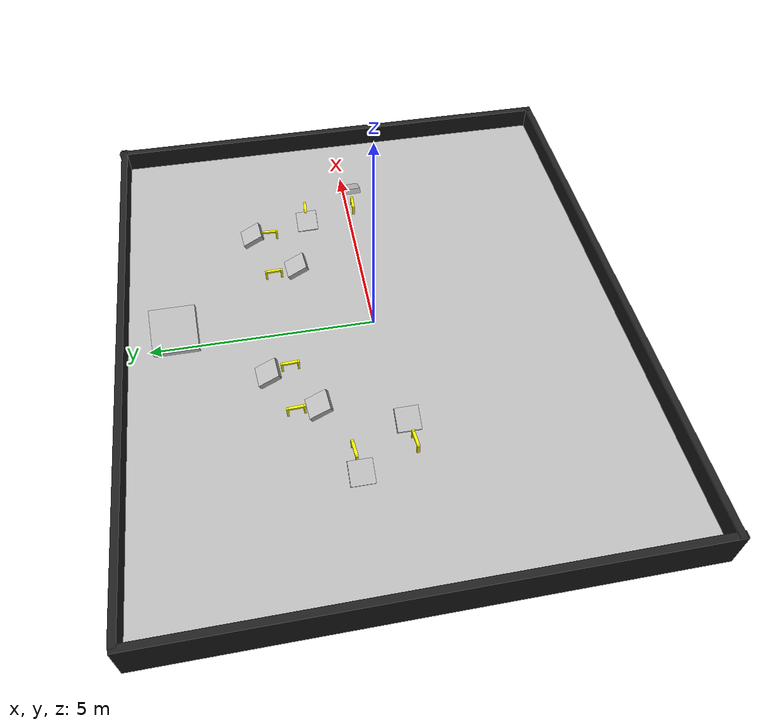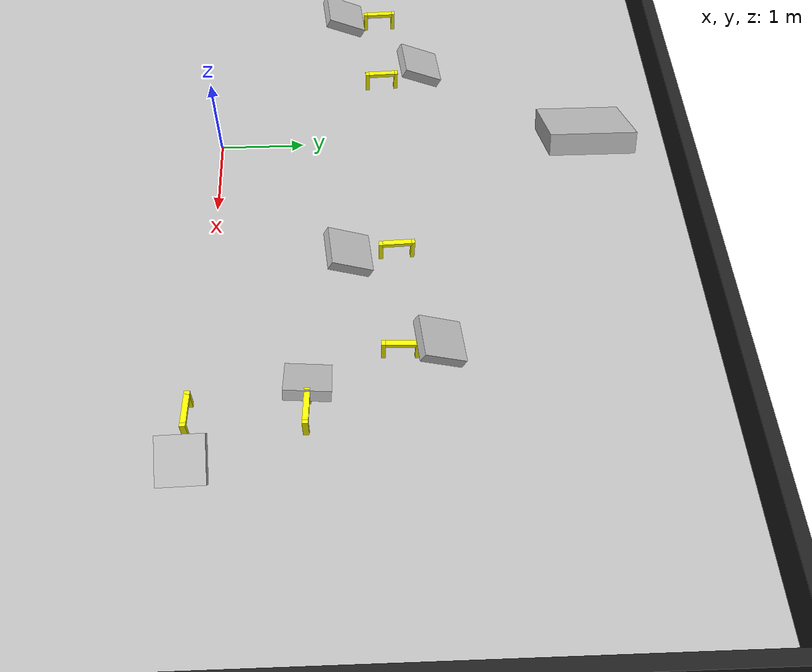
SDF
<sdf version="1.4">
  <world name="default">
    <scene>
      <ambient>0.8 0.8 0.8 1</ambient>
      <background>0.7 0.7 0.7 1</background>
      <shadows>true</shadows>
    </scene>

    <!-- A global light source -->
    <include>
      <uri>model://sun</uri>
      <pose> -2.0 2.0 2.0 0 0 0</pose>
    </include>

  <!-- Piso da sala - circuito -->
    <include>
      <uri>model://corrida_de_obstaculos/pisosala</uri>
      <pose> 0 0 0 0 0 -1.57</pose>
    </include>

  <!-- Parede da sala - circuito -->
    <include>
      <uri>model://corrida_de_obstaculos/parede</uri>
      <pose> 0 0 0 0 0 0</pose>
    </include>

 <!--  trave_1 -->
    <include>
      <uri>model://corrida_de_obstaculos/traves/trave_1</uri>
      <pose> -3.43 -0.26 0.16 0 0 -1.48</pose>
    </include>

 <!--  trave_2 -->
    <include>
      <uri>model://corrida_de_obstaculos/traves/trave_2</uri>
      <pose> -3.44 0.98 0.16 0 0 -1.48</pose>
    </include>

 <!--  trave_3 -->
    <include>
      <uri>model://corrida_de_obstaculos/traves/trave_3</uri>
      <pose> -2.15 2.13 0.16 0 0 -3.1</pose>
    </include>

 <!--  trave_4 -->
    <include>
      <uri>model://corrida_de_obstaculos/traves/trave_4</uri>
      <pose> -0.99 2.12 0.16 0 0 -3.10</pose>
    </include>

 <!--  trave_5 -->
    <include>
      <uri>model://corrida_de_obstaculos/traves/trave_5</uri>
      <pose> 1.77 2.19 0.16 0 0 -3.10</pose>
    </include>

 <!--  trave_6 -->
    <include>
      <uri>model://corrida_de_obstaculos/traves/trave_6</uri>
      <pose> 3.12 2.17 0.16 0 0 3.10</pose>
    </include>

 <!--  trave_7 -->
    <include>
      <uri>model://corrida_de_obstaculos/traves/trave_7</uri>
      <pose> 3.70 1.08 0.16 0 0 -1.62</pose>
    </include>

 <!--  trave_8 -->
    <include>
      <uri>model://corrida_de_obstaculos/traves/trave_8</uri>
      <pose> 3.69 -0.13 0.16 0 0 -1.62</pose>
    </include>

 <!--  creeper_10  -->
    <include>
      <uri>model://corrida_de_obstaculos/creepers/creeper_10</uri>
      <pose> -2.79 -0.19 0.15 0 -0.45 0</pose>
    </include>

 <!--  creeper_20  -->
    <include>
      <uri>model://corrida_de_obstaculos/creepers/creeper_20</uri>
      <pose> -3.83 0.94 0.15 0 -0.45 0</pose>
    </include>

 <!--  creeper_30  -->
    <include>
      <uri>model://corrida_de_obstaculos/creepers/creeper_30</uri>
      <pose> -2.16 1.51 0.15 0 -0.45 -1.48</pose>
    </include>

 <!--  creeper_40  -->
    <include>
      <uri>model://corrida_de_obstaculos/creepers/creeper_40</uri>
      <pose> -1.16 2.46 0.15 0 -0.45 -1.48</pose>
    </include>

 <!--  creeper_50  -->
    <include>
      <uri>model://corrida_de_obstaculos/creepers/creeper_50</uri>
      <pose> 1.86 1.50 0.15 0 -0.45 -1.48</pose>
    </include>

 <!--  creeper_60  -->
    <include>
      <uri>model://corrida_de_obstaculos/creepers/creeper_50</uri>
      <pose> 3.08 2.44 0.15 0 -0.45 -1.48</pose>
    </include>

 <!--  creeper_70  -->
    <include>
      <uri>model://corrida_de_obstaculos/creepers/creeper_70</uri>
      <pose> 3.43 1.08 0.15 3.06 -0.45 0</pose>
    </include>

 <!--  creeper_80  -->
    <include>
      <uri>model://corrida_de_obstaculos/creepers/creeper_80</uri>
      <pose> 4.33 -0.14 0.15 0 -0.45 -3.12</pose>
    </include>

 <!--  creeper_100 -->
    <include>
      <uri>model://corrida_de_obstaculos/creepers/creeper_100</uri>
      <pose> 0.29 4.39 0.25 0 -0.47 0</pose>
    </include>

    <physics type="ode">
      <real_time_update_rate>1000.0</real_time_update_rate>
      <max_step_size>0.001</max_step_size>
      <real_time_factor>1</real_time_factor>
      <ode>
        <solver>
          <type>quick</type>
          <iters>150</iters>
          <precon_iters>0</precon_iters>
          <sor>1.400000</sor>
          <use_dynamic_moi_rescaling>1</use_dynamic_moi_rescaling>
        </solver>
        <constraints>
          <cfm>0.00001</cfm>
          <erp>0.2</erp>
          <contact_max_correcting_vel>2000.000000</contact_max_correcting_vel>
          <contact_surface_layer>0.01000</contact_surface_layer>
        </constraints>
      </ode>
    </physics>

    <gui fullscreen='0'>
      <camera name='user_camera'>
        <pose frame=''>0.238775 -6.8831 10.8485 -0 0.979642 1.5602</pose>
        <view_controller>orbit</view_controller>
        <projection_type>perspective</projection_type>
      </camera>
    </gui>

  </world>

</sdf>

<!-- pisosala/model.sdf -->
<sdf version="1.6">
  <model name="pisosala_forca">
    <static>true</static>
    <link name="course_link">
      <collision name="course_collision">
        <geometry>
          <plane>
            <normal>0 0 1</normal>
            <size>10 13</size>
          </plane>
        </geometry>
        <surface>
          <friction>
            <ode>
              <mu>100</mu>
              <mu2>50</mu2>
            </ode>
          </friction>
        </surface>
      </collision>
      <visual name="course_visual">
        <cast_shadows>false</cast_shadows>
        <geometry>
          <mesh>
            <uri>model://forca/pisosala/materials/scripts/piso.dae</uri>
            <scale>1 1 1</scale>
          </mesh>
        </geometry>
      </visual>
    </link>
  </model>
</sdf>

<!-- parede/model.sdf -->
<sdf version='1.6'>
  <model name='parede'>
    <link name='Wall_0'>
      <pose frame=''>-0.004951 -5.56026 0 0 -0 0</pose>
      <self_collide>0</self_collide>
      <enable_wind>0</enable_wind>
      <kinematic>0</kinematic>
      <inertial>
        <inertia>
          <ixx>0</ixx>
          <ixy>0</ixy>
          <ixz>0</ixz>
          <iyy>0</iyy>
          <iyz>0</iyz>
          <izz>0</izz>
        </inertia>
        <mass>0</mass>
        <pose frame=''>0 0 0 0 -0 0</pose>
      </inertial>
      <gravity>1</gravity>
      <visual name='Wall_0_Visual'>
        <pose frame=''>0 0 0 0 -0 0</pose>
        <geometry>
          <box>
            <size>13.1161 0.15 1.0</size>
          </box>
        </geometry>
        <material>
          <script>
            <uri>file://media/materials/scripts/gazebo.material</uri>
            <name>Gazebo/Black</name>
          </script>
          <ambient>0 0 0 1</ambient>
          <shader type='vertex'>
            <normal_map>__default__</normal_map>
          </shader>
          <diffuse>0 0 0 1</diffuse>
          <specular>0 0 0 1</specular>
          <emissive>0 0 0 1</emissive>
        </material>
        <meta>
          <layer>0</layer>
        </meta>
        <transparency>0</transparency>
        <cast_shadows>1</cast_shadows>
      </visual>
      <collision name='Wall_0_Collision'>
        <laser_retro>0</laser_retro>
        <max_contacts>10</max_contacts>
        <pose frame=''>0 0 0 0 -0 0</pose>
        <geometry>
          <box>
            <size>13.1161 0.15 1.0</size>
          </box>
        </geometry>
        <surface>
          <friction>
            <ode>
              <mu>1</mu>
              <mu2>1</mu2>
              <fdir1>0 0 0</fdir1>
              <slip1>0</slip1>
              <slip2>0</slip2>
            </ode>
            <torsional>
              <coefficient>1</coefficient>
              <patch_radius>0</patch_radius>
              <surface_radius>0</surface_radius>
              <use_patch_radius>1</use_patch_radius>
              <ode>
                <slip>0</slip>
              </ode>
            </torsional>
          </friction>
          <bounce>
            <restitution_coefficient>0</restitution_coefficient>
            <threshold>1e+06</threshold>
          </bounce>
          <contact>
            <collide_without_contact>0</collide_without_contact>
            <collide_without_contact_bitmask>1</collide_without_contact_bitmask>
            <collide_bitmask>1</collide_bitmask>
            <ode>
              <soft_cfm>0</soft_cfm>
              <soft_erp>0.2</soft_erp>
              <kp>1e+13</kp>
              <kd>1</kd>
              <max_vel>0.01</max_vel>
              <min_depth>0</min_depth>
            </ode>
            <bullet>
              <split_impulse>1</split_impulse>
              <split_impulse_penetration_threshold>-0.01</split_impulse_penetration_threshold>
              <soft_cfm>0</soft_cfm>
              <soft_erp>0.2</soft_erp>
              <kp>1e+13</kp>
              <kd>1</kd>
            </bullet>
          </contact>
        </surface>
      </collision>
    </link>
    <link name='Wall_1'>
      <pose frame=''>0.061052 5.53717 0 0 -0 3.14</pose>
      <self_collide>0</self_collide>
      <enable_wind>0</enable_wind>
      <kinematic>0</kinematic>
      <inertial>
        <inertia>
          <ixx>0</ixx>
          <ixy>0</ixy>
          <ixz>0</ixz>
          <iyy>0</iyy>
          <iyz>0</iyz>
          <izz>0</izz>
        </inertia>
        <mass>0</mass>
        <pose frame=''>0 0 0 0 -0 0</pose>
      </inertial>
      <gravity>1</gravity>
      <visual name='Wall_1_Visual'>
        <pose frame=''>0 0 0 0 -0 0</pose>
        <geometry>
          <box>
            <size>13.1161 0.15 1.0</size>
          </box>
        </geometry>
        <material>
          <script>
            <uri>file://media/materials/scripts/gazebo.material</uri>
            <name>Gazebo/Black</name>
          </script>
          <ambient>0 0 0 1</ambient>
          <shader type='vertex'>
            <normal_map>__default__</normal_map>
          </shader>
          <diffuse>0 0 0 1</diffuse>
          <specular>0 0 0 1</specular>
          <emissive>0 0 0 1</emissive>
        </material>
        <meta>
          <layer>0</layer>
        </meta>
        <transparency>0</transparency>
        <cast_shadows>1</cast_shadows>
      </visual>
      <collision name='Wall_1_Collision'>
        <laser_retro>0</laser_retro>
        <max_contacts>10</max_contacts>
        <pose frame=''>0 0 0 0 -0 0</pose>
        <geometry>
          <box>
            <size>13.1161 0.15 1.0</size>
          </box>
        </geometry>
        <surface>
          <friction>
            <ode>
              <mu>1</mu>
              <mu2>1</mu2>
              <fdir1>0 0 0</fdir1>
              <slip1>0</slip1>
              <slip2>0</slip2>
            </ode>
            <torsional>
              <coefficient>1</coefficient>
              <patch_radius>0</patch_radius>
              <surface_radius>0</surface_radius>
              <use_patch_radius>1</use_patch_radius>
              <ode>
                <slip>0</slip>
              </ode>
            </torsional>
          </friction>
          <bounce>
            <restitution_coefficient>0</restitution_coefficient>
            <threshold>1e+06</threshold>
          </bounce>
          <contact>
            <collide_without_contact>0</collide_without_contact>
            <collide_without_contact_bitmask>1</collide_without_contact_bitmask>
            <collide_bitmask>1</collide_bitmask>
            <ode>
              <soft_cfm>0</soft_cfm>
              <soft_erp>0.2</soft_erp>
              <kp>1e+13</kp>
              <kd>1</kd>
              <max_vel>0.01</max_vel>
              <min_depth>0</min_depth>
            </ode>
            <bullet>
              <split_impulse>1</split_impulse>
              <split_impulse_penetration_threshold>-0.01</split_impulse_penetration_threshold>
              <soft_cfm>0</soft_cfm>
              <soft_erp>0.2</soft_erp>
              <kp>1e+13</kp>
              <kd>1</kd>
            </bullet>
          </contact>
        </surface>
      </collision>
    </link>
    <link name='Wall_2'>
      <pose frame=''>6.5 0.005899 0 0 -0 1.57</pose>
      <self_collide>0</self_collide>
      <enable_wind>0</enable_wind>
      <kinematic>0</kinematic>
      <inertial>
        <inertia>
          <ixx>0</ixx>
          <ixy>0</ixy>
          <ixz>0</ixz>
          <iyy>0</iyy>
          <iyz>0</iyz>
          <izz>0</izz>
        </inertia>
        <mass>0</mass>
        <pose frame=''>0 0 0 0 -0 0</pose>
      </inertial>
      <gravity>1</gravity>
      <visual name='Wall_2_Visual'>
        <pose frame=''>0 0 0 0 -0 0</pose>
        <geometry>
          <box>
            <size>11.2703 0.15 1.0</size>
          </box>
        </geometry>
        <material>
          <script>
            <uri>file://media/materials/scripts/gazebo.material</uri>
            <name>Gazebo/Black</name>
          </script>
          <ambient>0 0 0 1</ambient>
          <shader type='vertex'>
            <normal_map>__default__</normal_map>
          </shader>
          <diffuse>0 0 0 1</diffuse>
          <specular>0 0 0 1</specular>
          <emissive>0 0 0 1</emissive>
        </material>
        <meta>
          <layer>0</layer>
        </meta>
        <transparency>0</transparency>
        <cast_shadows>1</cast_shadows>
      </visual>
      <collision name='Wall_2_Collision'>
        <laser_retro>0</laser_retro>
        <max_contacts>10</max_contacts>
        <pose frame=''>0 0 0 0 -0 0</pose>
        <geometry>
          <box>
            <size>11.2703 0.15 1.0</size>
          </box>
        </geometry>
        <surface>
          <friction>
            <ode>
              <mu>1</mu>
              <mu2>1</mu2>
              <fdir1>0 0 0</fdir1>
              <slip1>0</slip1>
              <slip2>0</slip2>
            </ode>
            <torsional>
              <coefficient>1</coefficient>
              <patch_radius>0</patch_radius>
              <surface_radius>0</surface_radius>
              <use_patch_radius>1</use_patch_radius>
              <ode>
                <slip>0</slip>
              </ode>
            </torsional>
          </friction>
          <bounce>
            <restitution_coefficient>0</restitution_coefficient>
            <threshold>1e+06</threshold>
          </bounce>
          <contact>
            <collide_without_contact>0</collide_without_contact>
            <collide_without_contact_bitmask>1</collide_without_contact_bitmask>
            <collide_bitmask>1</collide_bitmask>
            <ode>
              <soft_cfm>0</soft_cfm>
              <soft_erp>0.2</soft_erp>
              <kp>1e+13</kp>
              <kd>1</kd>
              <max_vel>0.01</max_vel>
              <min_depth>0</min_depth>
            </ode>
            <bullet>
              <split_impulse>1</split_impulse>
              <split_impulse_penetration_threshold>-0.01</split_impulse_penetration_threshold>
              <soft_cfm>0</soft_cfm>
              <soft_erp>0.2</soft_erp>
              <kp>1e+13</kp>
              <kd>1</kd>
            </bullet>
          </contact>
        </surface>
      </collision>
    </link>
    <link name='Wall_3'>
      <pose frame=''>-6.49998 -0.025026 0 0 0 -1.57</pose>
      <self_collide>0</self_collide>
      <enable_wind>0</enable_wind>
      <kinematic>0</kinematic>
      <inertial>
        <inertia>
          <ixx>0</ixx>
          <ixy>0</ixy>
          <ixz>0</ixz>
          <iyy>0</iyy>
          <iyz>0</iyz>
          <izz>0</izz>
        </inertia>
        <mass>0</mass>
        <pose frame=''>0 0 0 0 -0 0</pose>
      </inertial>
      <gravity>1</gravity>
      <visual name='Wall_3_Visual'>
        <pose frame=''>0 0 0 0 -0 0</pose>
        <geometry>
          <box>
            <size>11.2703 0.15 1.0</size>
          </box>
        </geometry>
        <material>
          <script>
            <uri>file://media/materials/scripts/gazebo.material</uri>
            <name>Gazebo/Black</name>
          </script>
          <ambient>0 0 0 1</ambient>
          <shader type='vertex'>
            <normal_map>__default__</normal_map>
          </shader>
          <diffuse>0 0 0 1</diffuse>
          <specular>0 0 0 1</specular>
          <emissive>0 0 0 1</emissive>
        </material>
        <meta>
          <layer>0</layer>
        </meta>
        <transparency>0</transparency>
        <cast_shadows>1</cast_shadows>
      </visual>
      <collision name='Wall_3_Collision'>
        <laser_retro>0</laser_retro>
        <max_contacts>10</max_contacts>
        <pose frame=''>0 0 0 0 -0 0</pose>
        <geometry>
          <box>
            <size>11.2703 0.15 1.0</size>
          </box>
        </geometry>
        <surface>
          <friction>
            <ode>
              <mu>1</mu>
              <mu2>1</mu2>
              <fdir1>0 0 0</fdir1>
              <slip1>0</slip1>
              <slip2>0</slip2>
            </ode>
            <torsional>
              <coefficient>1</coefficient>
              <patch_radius>0</patch_radius>
              <surface_radius>0</surface_radius>
              <use_patch_radius>1</use_patch_radius>
              <ode>
                <slip>0</slip>
              </ode>
            </torsional>
          </friction>
          <bounce>
            <restitution_coefficient>0</restitution_coefficient>
            <threshold>1e+06</threshold>
          </bounce>
          <contact>
            <collide_without_contact>0</collide_without_contact>
            <collide_without_contact_bitmask>1</collide_without_contact_bitmask>
            <collide_bitmask>1</collide_bitmask>
            <ode>
              <soft_cfm>0</soft_cfm>
              <soft_erp>0.2</soft_erp>
              <kp>1e+13</kp>
              <kd>1</kd>
              <max_vel>0.01</max_vel>
              <min_depth>0</min_depth>
            </ode>
            <bullet>
              <split_impulse>1</split_impulse>
              <split_impulse_penetration_threshold>-0.01</split_impulse_penetration_threshold>
              <soft_cfm>0</soft_cfm>
              <soft_erp>0.2</soft_erp>
              <kp>1e+13</kp>
              <kd>1</kd>
            </bullet>
          </contact>
        </surface>
      </collision>
    </link>
    <static>1</static>
    <allow_auto_disable>1</allow_auto_disable>
  </model>
</sdf>

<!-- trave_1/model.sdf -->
<sdf version='1.7'>
  <model name='trave_1'>
   <link name='link_clone'>
      <inertial>
        <mass>0.05</mass>
        <inertia>
          <ixx>0.00026237</ixx>
          <ixy>0</ixy>
          <ixz>0</ixz>
          <iyy>0.00026976</iyy>
          <iyz>0</iyz>
          <izz>2.415e-05</izz>
        </inertia>
        <pose>0 0 0 0 -0 0</pose>
      </inertial>
      <self_collide>0</self_collide>
      <enable_wind>0</enable_wind>
      <kinematic>0</kinematic>
      <pose>0.003921 0.29924 -0.033189 0 -3e-06 -2.6e-05</pose>
      <gravity>1</gravity>
      <visual name='visual'>
        <geometry>
          <box>
            <size>0.061532 0.044841 0.246895</size>
          </box>
        </geometry>
        <material>
          <script>
            <name>Gazebo/Grey</name>
            <uri>file://media/materials/scripts/gazebo.material</uri>
          </script>
          <shader type='pixel'>
            <normal_map>__default__</normal_map>
          </shader>
          <ambient>1 1 0 0</ambient>
          <diffuse>1 1 0 1</diffuse>
          <specular>1 1 0 1</specular>
          <emissive>0 0 0 1</emissive>
        </material>
        <pose>0 0 0 0 -0 0</pose>
        <transparency>0</transparency>
        <cast_shadows>1</cast_shadows>
      </visual>
      <collision name='collision'>
        <laser_retro>0</laser_retro>
        <max_contacts>10</max_contacts>
        <pose>0 0 0 0 -0 0</pose>
        <geometry>
          <box>
            <size>0.061532 0.044841 0.246895</size>
          </box>
        </geometry>
        <surface>
          <friction>
            <ode>
              <mu>1</mu>
              <mu2>1</mu2>
              <fdir1>0 0 0</fdir1>
              <slip1>0</slip1>
              <slip2>0</slip2>
            </ode>
            <torsional>
              <coefficient>1</coefficient>
              <patch_radius>0</patch_radius>
              <surface_radius>0</surface_radius>
              <use_patch_radius>1</use_patch_radius>
              <ode>
                <slip>0</slip>
              </ode>
            </torsional>
          </friction>
          <bounce>
            <restitution_coefficient>0</restitution_coefficient>
            <threshold>1e+06</threshold>
          </bounce>
          <contact>
            <collide_without_contact>0</collide_without_contact>
            <collide_without_contact_bitmask>1</collide_without_contact_bitmask>
            <collide_bitmask>1</collide_bitmask>
            <ode>
              <soft_cfm>0</soft_cfm>
              <soft_erp>0.2</soft_erp>
              <kp>1e+13</kp>
              <kd>1</kd>
              <max_vel>0.01</max_vel>
              <min_depth>0</min_depth>
            </ode>
            <bullet>
              <split_impulse>1</split_impulse>
              <split_impulse_penetration_threshold>-0.01</split_impulse_penetration_threshold>
              <soft_cfm>0</soft_cfm>
              <soft_erp>0.2</soft_erp>
              <kp>1e+13</kp>
              <kd>1</kd>
            </bullet>
          </contact>
        </surface>
      </collision>
    </link>
    <link name='link_clone_0'>
      <inertial>
        <mass>0.02</mass>
        <inertia>
          <ixx>0.00017985</ixx>
          <ixy>0</ixy>
          <ixz>0</ixz>
          <iyy>0.00018281</iyy>
          <iyz>0</iyz>
          <izz>9.66e-06</izz>
        </inertia>
        <pose>0 0 0 0 -0 0</pose>
      </inertial>
      <self_collide>0</self_collide>
      <enable_wind>0</enable_wind>
      <kinematic>0</kinematic>
      <pose>0.003572 0.115777 0.067162 -1.57167 -3e-06 -2.6e-05</pose>
      <gravity>1</gravity>
      <visual name='visual'>
        <geometry>
          <box>
            <size>0.061532 0.044841 0.325421</size>
          </box>
        </geometry>
        <material>
          <script>
            <name>Gazebo/Grey</name>
            <uri>file://media/materials/scripts/gazebo.material</uri>
          </script>
          <shader type='pixel'>
            <normal_map>__default__</normal_map>
          </shader>
          <ambient>1 1 0 0</ambient>
          <diffuse>1 1 0 1</diffuse>
          <specular>1 1 0 1</specular>
          <emissive>0 0 0 1</emissive>
        </material>
        <pose>0 0 0 0 -0 0</pose>
        <transparency>0</transparency>
        <cast_shadows>1</cast_shadows>
      </visual>
      <collision name='collision'>
        <laser_retro>0</laser_retro>
        <max_contacts>10</max_contacts>
        <pose>0 0 0 0 -0 0</pose>
        <geometry>
          <box>
            <size>0.061532 0.044841 0.325421</size>
          </box>
        </geometry>
        <surface>
          <friction>
            <ode>
              <mu>1</mu>
              <mu2>1</mu2>
              <fdir1>0 0 0</fdir1>
              <slip1>0</slip1>
              <slip2>0</slip2>
            </ode>
            <torsional>
              <coefficient>1</coefficient>
              <patch_radius>0</patch_radius>
              <surface_radius>0</surface_radius>
              <use_patch_radius>1</use_patch_radius>
              <ode>
                <slip>0</slip>
              </ode>
            </torsional>
          </friction>
          <bounce>
            <restitution_coefficient>0</restitution_coefficient>
            <threshold>1e+06</threshold>
          </bounce>
          <contact>
            <collide_without_contact>0</collide_without_contact>
            <collide_without_contact_bitmask>1</collide_without_contact_bitmask>
            <collide_bitmask>1</collide_bitmask>
            <ode>
              <soft_cfm>0</soft_cfm>
              <soft_erp>0.2</soft_erp>
              <kp>1e+13</kp>
              <kd>1</kd>
              <max_vel>0.01</max_vel>
              <min_depth>0</min_depth>
            </ode>
            <bullet>
              <split_impulse>1</split_impulse>
              <split_impulse_penetration_threshold>-0.01</split_impulse_penetration_threshold>
              <soft_cfm>0</soft_cfm>
              <soft_erp>0.2</soft_erp>
              <kp>1e+13</kp>
              <kd>1</kd>
            </bullet>
          </contact>
        </surface>
      </collision>
    </link>
    <link name='link_clone_clone'>
      <inertial>
        <mass>0.05</mass>
        <inertia>
          <ixx>0.00026237</ixx>
          <ixy>0</ixy>
          <ixz>0</ixz>
          <iyy>0.00026976</iyy>
          <iyz>0</iyz>
          <izz>2.415e-05</izz>
        </inertia>
        <pose>0 0 0 0 -0 0</pose>
      </inertial>
      <self_collide>0</self_collide>
      <enable_wind>0</enable_wind>
      <kinematic>0</kinematic>
      <pose>0.004273 -0.059266 -0.034475 0.021558 -4.2e-05 0.001742</pose>
      <gravity>1</gravity>
      <visual name='visual'>
        <geometry>
          <box>
            <size>0.061532 0.044841 0.246895</size>
          </box>
        </geometry>
        <material>
          <script>
            <name>Gazebo/Grey</name>
            <uri>file://media/materials/scripts/gazebo.material</uri>
          </script>
          <shader type='pixel'>
            <normal_map>__default__</normal_map>
          </shader>
          <ambient>1 1 0 0</ambient>
          <diffuse>1 1 0 1</diffuse>
          <specular>1 1 0 1</specular>
          <emissive>0 0 0 1</emissive>
        </material>
        <pose>0 0 0 0 -0 0</pose>
        <transparency>0</transparency>
        <cast_shadows>1</cast_shadows>
      </visual>
      <collision name='collision'>
        <laser_retro>0</laser_retro>
        <max_contacts>10</max_contacts>
        <pose>0 0 0 0 -0 0</pose>
        <geometry>
          <box>
            <size>0.061532 0.044841 0.246895</size>
          </box>
        </geometry>
        <surface>
          <friction>
            <ode>
              <mu>1</mu>
              <mu2>1</mu2>
              <fdir1>0 0 0</fdir1>
              <slip1>0</slip1>
              <slip2>0</slip2>
            </ode>
            <torsional>
              <coefficient>1</coefficient>
              <patch_radius>0</patch_radius>
              <surface_radius>0</surface_radius>
              <use_patch_radius>1</use_patch_radius>
              <ode>
                <slip>0</slip>
              </ode>
            </torsional>
          </friction>
          <bounce>
            <restitution_coefficient>0</restitution_coefficient>
            <threshold>1e+06</threshold>
          </bounce>
          <contact>
            <collide_without_contact>0</collide_without_contact>
            <collide_without_contact_bitmask>1</collide_without_contact_bitmask>
            <collide_bitmask>1</collide_bitmask>
            <ode>
              <soft_cfm>0</soft_cfm>
              <soft_erp>0.2</soft_erp>
              <kp>1e+13</kp>
              <kd>1</kd>
              <max_vel>0.01</max_vel>
              <min_depth>0</min_depth>
            </ode>
            <bullet>
              <split_impulse>1</split_impulse>
              <split_impulse_penetration_threshold>-0.01</split_impulse_penetration_threshold>
              <soft_cfm>0</soft_cfm>
              <soft_erp>0.2</soft_erp>
              <kp>1e+13</kp>
              <kd>1</kd>
            </bullet>
          </contact>
        </surface>
      </collision>
    </link>
    <joint name='link_clone_0_JOINT_0' type='fixed'>
      <parent>link_clone_0</parent>
      <child>link_clone_clone</child>
      <pose>0 0 0 0 -0 0</pose>
      <physics>
        <ode>
          <limit>
            <cfm>0</cfm>
            <erp>0.2</erp>
          </limit>
          <suspension>
            <cfm>0</cfm>
            <erp>0.2</erp>
          </suspension>
        </ode>
      </physics>
    </joint>
    <joint name='link_clone_0_JOINT_1' type='fixed'>
      <parent>link_clone_0</parent>
      <child>link_clone</child>
      <pose>0 0 0 0 -0 0</pose>
      <physics>
        <ode>
          <limit>
            <cfm>0</cfm>
            <erp>0.2</erp>
          </limit>
          <suspension>
            <cfm>0</cfm>
            <erp>0.2</erp>
          </suspension>
        </ode>
      </physics>
    </joint>
    <static>0</static>
    <allow_auto_disable>1</allow_auto_disable>
  </model>
</sdf>

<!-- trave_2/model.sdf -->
<sdf version='1.7'>
  <model name='trave_2'>
   <link name='link_clone'>
      <inertial>
        <mass>0.05</mass>
        <inertia>
          <ixx>0.00026237</ixx>
          <ixy>0</ixy>
          <ixz>0</ixz>
          <iyy>0.00026976</iyy>
          <iyz>0</iyz>
          <izz>2.415e-05</izz>
        </inertia>
        <pose>0 0 0 0 -0 0</pose>
      </inertial>
      <self_collide>0</self_collide>
      <enable_wind>0</enable_wind>
      <kinematic>0</kinematic>
      <pose>0.003921 0.29924 -0.033189 0 -3e-06 -2.6e-05</pose>
      <gravity>1</gravity>
      <visual name='visual'>
        <geometry>
          <box>
            <size>0.061532 0.044841 0.246895</size>
          </box>
        </geometry>
        <material>
          <script>
            <name>Gazebo/Grey</name>
            <uri>file://media/materials/scripts/gazebo.material</uri>
          </script>
          <shader type='pixel'>
            <normal_map>__default__</normal_map>
          </shader>
          <ambient>1 1 0 0</ambient>
          <diffuse>1 1 0 1</diffuse>
          <specular>1 1 0 1</specular>
          <emissive>0 0 0 1</emissive>
        </material>
        <pose>0 0 0 0 -0 0</pose>
        <transparency>0</transparency>
        <cast_shadows>1</cast_shadows>
      </visual>
      <collision name='collision'>
        <laser_retro>0</laser_retro>
        <max_contacts>10</max_contacts>
        <pose>0 0 0 0 -0 0</pose>
        <geometry>
          <box>
            <size>0.061532 0.044841 0.246895</size>
          </box>
        </geometry>
        <surface>
          <friction>
            <ode>
              <mu>1</mu>
              <mu2>1</mu2>
              <fdir1>0 0 0</fdir1>
              <slip1>0</slip1>
              <slip2>0</slip2>
            </ode>
            <torsional>
              <coefficient>1</coefficient>
              <patch_radius>0</patch_radius>
              <surface_radius>0</surface_radius>
              <use_patch_radius>1</use_patch_radius>
              <ode>
                <slip>0</slip>
              </ode>
            </torsional>
          </friction>
          <bounce>
            <restitution_coefficient>0</restitution_coefficient>
            <threshold>1e+06</threshold>
          </bounce>
          <contact>
            <collide_without_contact>0</collide_without_contact>
            <collide_without_contact_bitmask>1</collide_without_contact_bitmask>
            <collide_bitmask>1</collide_bitmask>
            <ode>
              <soft_cfm>0</soft_cfm>
              <soft_erp>0.2</soft_erp>
              <kp>1e+13</kp>
              <kd>1</kd>
              <max_vel>0.01</max_vel>
              <min_depth>0</min_depth>
            </ode>
            <bullet>
              <split_impulse>1</split_impulse>
              <split_impulse_penetration_threshold>-0.01</split_impulse_penetration_threshold>
              <soft_cfm>0</soft_cfm>
              <soft_erp>0.2</soft_erp>
              <kp>1e+13</kp>
              <kd>1</kd>
            </bullet>
          </contact>
        </surface>
      </collision>
    </link>
    <link name='link_clone_0'>
      <inertial>
        <mass>0.02</mass>
        <inertia>
          <ixx>0.00017985</ixx>
          <ixy>0</ixy>
          <ixz>0</ixz>
          <iyy>0.00018281</iyy>
          <iyz>0</iyz>
          <izz>9.66e-06</izz>
        </inertia>
        <pose>0 0 0 0 -0 0</pose>
      </inertial>
      <self_collide>0</self_collide>
      <enable_wind>0</enable_wind>
      <kinematic>0</kinematic>
      <pose>0.003572 0.115777 0.067162 -1.57167 -3e-06 -2.6e-05</pose>
      <gravity>1</gravity>
      <visual name='visual'>
        <geometry>
          <box>
            <size>0.061532 0.044841 0.325421</size>
          </box>
        </geometry>
        <material>
          <script>
            <name>Gazebo/Grey</name>
            <uri>file://media/materials/scripts/gazebo.material</uri>
          </script>
          <shader type='pixel'>
            <normal_map>__default__</normal_map>
          </shader>
          <ambient>1 1 0 0</ambient>
          <diffuse>1 1 0 1</diffuse>
          <specular>1 1 0 1</specular>
          <emissive>0 0 0 1</emissive>
        </material>
        <pose>0 0 0 0 -0 0</pose>
        <transparency>0</transparency>
        <cast_shadows>1</cast_shadows>
      </visual>
      <collision name='collision'>
        <laser_retro>0</laser_retro>
        <max_contacts>10</max_contacts>
        <pose>0 0 0 0 -0 0</pose>
        <geometry>
          <box>
            <size>0.061532 0.044841 0.325421</size>
          </box>
        </geometry>
        <surface>
          <friction>
            <ode>
              <mu>1</mu>
              <mu2>1</mu2>
              <fdir1>0 0 0</fdir1>
              <slip1>0</slip1>
              <slip2>0</slip2>
            </ode>
            <torsional>
              <coefficient>1</coefficient>
              <patch_radius>0</patch_radius>
              <surface_radius>0</surface_radius>
              <use_patch_radius>1</use_patch_radius>
              <ode>
                <slip>0</slip>
              </ode>
            </torsional>
          </friction>
          <bounce>
            <restitution_coefficient>0</restitution_coefficient>
            <threshold>1e+06</threshold>
          </bounce>
          <contact>
            <collide_without_contact>0</collide_without_contact>
            <collide_without_contact_bitmask>1</collide_without_contact_bitmask>
            <collide_bitmask>1</collide_bitmask>
            <ode>
              <soft_cfm>0</soft_cfm>
              <soft_erp>0.2</soft_erp>
              <kp>1e+13</kp>
              <kd>1</kd>
              <max_vel>0.01</max_vel>
              <min_depth>0</min_depth>
            </ode>
            <bullet>
              <split_impulse>1</split_impulse>
              <split_impulse_penetration_threshold>-0.01</split_impulse_penetration_threshold>
              <soft_cfm>0</soft_cfm>
              <soft_erp>0.2</soft_erp>
              <kp>1e+13</kp>
              <kd>1</kd>
            </bullet>
          </contact>
        </surface>
      </collision>
    </link>
    <link name='link_clone_clone'>
      <inertial>
        <mass>0.05</mass>
        <inertia>
          <ixx>0.00026237</ixx>
          <ixy>0</ixy>
          <ixz>0</ixz>
          <iyy>0.00026976</iyy>
          <iyz>0</iyz>
          <izz>2.415e-05</izz>
        </inertia>
        <pose>0 0 0 0 -0 0</pose>
      </inertial>
      <self_collide>0</self_collide>
      <enable_wind>0</enable_wind>
      <kinematic>0</kinematic>
      <pose>0.004273 -0.059266 -0.034475 0.021558 -4.2e-05 0.001742</pose>
      <gravity>1</gravity>
      <visual name='visual'>
        <geometry>
          <box>
            <size>0.061532 0.044841 0.246895</size>
          </box>
        </geometry>
        <material>
          <script>
            <name>Gazebo/Grey</name>
            <uri>file://media/materials/scripts/gazebo.material</uri>
          </script>
          <shader type='pixel'>
            <normal_map>__default__</normal_map>
          </shader>
          <ambient>1 1 0 0</ambient>
          <diffuse>1 1 0 1</diffuse>
          <specular>1 1 0 1</specular>
          <emissive>0 0 0 1</emissive>
        </material>
        <pose>0 0 0 0 -0 0</pose>
        <transparency>0</transparency>
        <cast_shadows>1</cast_shadows>
      </visual>
      <collision name='collision'>
        <laser_retro>0</laser_retro>
        <max_contacts>10</max_contacts>
        <pose>0 0 0 0 -0 0</pose>
        <geometry>
          <box>
            <size>0.061532 0.044841 0.246895</size>
          </box>
        </geometry>
        <surface>
          <friction>
            <ode>
              <mu>1</mu>
              <mu2>1</mu2>
              <fdir1>0 0 0</fdir1>
              <slip1>0</slip1>
              <slip2>0</slip2>
            </ode>
            <torsional>
              <coefficient>1</coefficient>
              <patch_radius>0</patch_radius>
              <surface_radius>0</surface_radius>
              <use_patch_radius>1</use_patch_radius>
              <ode>
                <slip>0</slip>
              </ode>
            </torsional>
          </friction>
          <bounce>
            <restitution_coefficient>0</restitution_coefficient>
            <threshold>1e+06</threshold>
          </bounce>
          <contact>
            <collide_without_contact>0</collide_without_contact>
            <collide_without_contact_bitmask>1</collide_without_contact_bitmask>
            <collide_bitmask>1</collide_bitmask>
            <ode>
              <soft_cfm>0</soft_cfm>
              <soft_erp>0.2</soft_erp>
              <kp>1e+13</kp>
              <kd>1</kd>
              <max_vel>0.01</max_vel>
              <min_depth>0</min_depth>
            </ode>
            <bullet>
              <split_impulse>1</split_impulse>
              <split_impulse_penetration_threshold>-0.01</split_impulse_penetration_threshold>
              <soft_cfm>0</soft_cfm>
              <soft_erp>0.2</soft_erp>
              <kp>1e+13</kp>
              <kd>1</kd>
            </bullet>
          </contact>
        </surface>
      </collision>
    </link>
    <joint name='link_clone_0_JOINT_0' type='fixed'>
      <parent>link_clone_0</parent>
      <child>link_clone_clone</child>
      <pose>0 0 0 0 -0 0</pose>
      <physics>
        <ode>
          <limit>
            <cfm>0</cfm>
            <erp>0.2</erp>
          </limit>
          <suspension>
            <cfm>0</cfm>
            <erp>0.2</erp>
          </suspension>
        </ode>
      </physics>
    </joint>
    <joint name='link_clone_0_JOINT_1' type='fixed'>
      <parent>link_clone_0</parent>
      <child>link_clone</child>
      <pose>0 0 0 0 -0 0</pose>
      <physics>
        <ode>
          <limit>
            <cfm>0</cfm>
            <erp>0.2</erp>
          </limit>
          <suspension>
            <cfm>0</cfm>
            <erp>0.2</erp>
          </suspension>
        </ode>
      </physics>
    </joint>
    <static>0</static>
    <allow_auto_disable>1</allow_auto_disable>
  </model>
</sdf>

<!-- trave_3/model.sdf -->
<sdf version='1.7'>
  <model name='trave_3'>
   <link name='link_clone'>
      <inertial>
        <mass>0.05</mass>
        <inertia>
          <ixx>0.00026237</ixx>
          <ixy>0</ixy>
          <ixz>0</ixz>
          <iyy>0.00026976</iyy>
          <iyz>0</iyz>
          <izz>2.415e-05</izz>
        </inertia>
        <pose>0 0 0 0 -0 0</pose>
      </inertial>
      <self_collide>0</self_collide>
      <enable_wind>0</enable_wind>
      <kinematic>0</kinematic>
      <pose>0.003921 0.29924 -0.033189 0 -3e-06 -2.6e-05</pose>
      <gravity>1</gravity>
      <visual name='visual'>
        <geometry>
          <box>
            <size>0.061532 0.044841 0.246895</size>
          </box>
        </geometry>
        <material>
          <script>
            <name>Gazebo/Grey</name>
            <uri>file://media/materials/scripts/gazebo.material</uri>
          </script>
          <shader type='pixel'>
            <normal_map>__default__</normal_map>
          </shader>
          <ambient>1 1 0 0</ambient>
          <diffuse>1 1 0 1</diffuse>
          <specular>1 1 0 1</specular>
          <emissive>0 0 0 1</emissive>
        </material>
        <pose>0 0 0 0 -0 0</pose>
        <transparency>0</transparency>
        <cast_shadows>1</cast_shadows>
      </visual>
      <collision name='collision'>
        <laser_retro>0</laser_retro>
        <max_contacts>10</max_contacts>
        <pose>0 0 0 0 -0 0</pose>
        <geometry>
          <box>
            <size>0.061532 0.044841 0.246895</size>
          </box>
        </geometry>
        <surface>
          <friction>
            <ode>
              <mu>1</mu>
              <mu2>1</mu2>
              <fdir1>0 0 0</fdir1>
              <slip1>0</slip1>
              <slip2>0</slip2>
            </ode>
            <torsional>
              <coefficient>1</coefficient>
              <patch_radius>0</patch_radius>
              <surface_radius>0</surface_radius>
              <use_patch_radius>1</use_patch_radius>
              <ode>
                <slip>0</slip>
              </ode>
            </torsional>
          </friction>
          <bounce>
            <restitution_coefficient>0</restitution_coefficient>
            <threshold>1e+06</threshold>
          </bounce>
          <contact>
            <collide_without_contact>0</collide_without_contact>
            <collide_without_contact_bitmask>1</collide_without_contact_bitmask>
            <collide_bitmask>1</collide_bitmask>
            <ode>
              <soft_cfm>0</soft_cfm>
              <soft_erp>0.2</soft_erp>
              <kp>1e+13</kp>
              <kd>1</kd>
              <max_vel>0.01</max_vel>
              <min_depth>0</min_depth>
            </ode>
            <bullet>
              <split_impulse>1</split_impulse>
              <split_impulse_penetration_threshold>-0.01</split_impulse_penetration_threshold>
              <soft_cfm>0</soft_cfm>
              <soft_erp>0.2</soft_erp>
              <kp>1e+13</kp>
              <kd>1</kd>
            </bullet>
          </contact>
        </surface>
      </collision>
    </link>
    <link name='link_clone_0'>
      <inertial>
        <mass>0.02</mass>
        <inertia>
          <ixx>0.00017985</ixx>
          <ixy>0</ixy>
          <ixz>0</ixz>
          <iyy>0.00018281</iyy>
          <iyz>0</iyz>
          <izz>9.66e-06</izz>
        </inertia>
        <pose>0 0 0 0 -0 0</pose>
      </inertial>
      <self_collide>0</self_collide>
      <enable_wind>0</enable_wind>
      <kinematic>0</kinematic>
      <pose>0.003572 0.115777 0.067162 -1.57167 -3e-06 -2.6e-05</pose>
      <gravity>1</gravity>
      <visual name='visual'>
        <geometry>
          <box>
            <size>0.061532 0.044841 0.325421</size>
          </box>
        </geometry>
        <material>
          <script>
            <name>Gazebo/Grey</name>
            <uri>file://media/materials/scripts/gazebo.material</uri>
          </script>
          <shader type='pixel'>
            <normal_map>__default__</normal_map>
          </shader>
          <ambient>1 1 0 0</ambient>
          <diffuse>1 1 0 1</diffuse>
          <specular>1 1 0 1</specular>
          <emissive>0 0 0 1</emissive>
        </material>
        <pose>0 0 0 0 -0 0</pose>
        <transparency>0</transparency>
        <cast_shadows>1</cast_shadows>
      </visual>
      <collision name='collision'>
        <laser_retro>0</laser_retro>
        <max_contacts>10</max_contacts>
        <pose>0 0 0 0 -0 0</pose>
        <geometry>
          <box>
            <size>0.061532 0.044841 0.325421</size>
          </box>
        </geometry>
        <surface>
          <friction>
            <ode>
              <mu>1</mu>
              <mu2>1</mu2>
              <fdir1>0 0 0</fdir1>
              <slip1>0</slip1>
              <slip2>0</slip2>
            </ode>
            <torsional>
              <coefficient>1</coefficient>
              <patch_radius>0</patch_radius>
              <surface_radius>0</surface_radius>
              <use_patch_radius>1</use_patch_radius>
              <ode>
                <slip>0</slip>
              </ode>
            </torsional>
          </friction>
          <bounce>
            <restitution_coefficient>0</restitution_coefficient>
            <threshold>1e+06</threshold>
          </bounce>
          <contact>
            <collide_without_contact>0</collide_without_contact>
            <collide_without_contact_bitmask>1</collide_without_contact_bitmask>
            <collide_bitmask>1</collide_bitmask>
            <ode>
              <soft_cfm>0</soft_cfm>
              <soft_erp>0.2</soft_erp>
              <kp>1e+13</kp>
              <kd>1</kd>
              <max_vel>0.01</max_vel>
              <min_depth>0</min_depth>
            </ode>
            <bullet>
              <split_impulse>1</split_impulse>
              <split_impulse_penetration_threshold>-0.01</split_impulse_penetration_threshold>
              <soft_cfm>0</soft_cfm>
              <soft_erp>0.2</soft_erp>
              <kp>1e+13</kp>
              <kd>1</kd>
            </bullet>
          </contact>
        </surface>
      </collision>
    </link>
    <link name='link_clone_clone'>
      <inertial>
        <mass>0.05</mass>
        <inertia>
          <ixx>0.00026237</ixx>
          <ixy>0</ixy>
          <ixz>0</ixz>
          <iyy>0.00026976</iyy>
          <iyz>0</iyz>
          <izz>2.415e-05</izz>
        </inertia>
        <pose>0 0 0 0 -0 0</pose>
      </inertial>
      <self_collide>0</self_collide>
      <enable_wind>0</enable_wind>
      <kinematic>0</kinematic>
      <pose>0.004273 -0.059266 -0.034475 0.021558 -4.2e-05 0.001742</pose>
      <gravity>1</gravity>
      <visual name='visual'>
        <geometry>
          <box>
            <size>0.061532 0.044841 0.246895</size>
          </box>
        </geometry>
        <material>
          <script>
            <name>Gazebo/Grey</name>
            <uri>file://media/materials/scripts/gazebo.material</uri>
          </script>
          <shader type='pixel'>
            <normal_map>__default__</normal_map>
          </shader>
          <ambient>1 1 0 0</ambient>
          <diffuse>1 1 0 1</diffuse>
          <specular>1 1 0 1</specular>
          <emissive>0 0 0 1</emissive>
        </material>
        <pose>0 0 0 0 -0 0</pose>
        <transparency>0</transparency>
        <cast_shadows>1</cast_shadows>
      </visual>
      <collision name='collision'>
        <laser_retro>0</laser_retro>
        <max_contacts>10</max_contacts>
        <pose>0 0 0 0 -0 0</pose>
        <geometry>
          <box>
            <size>0.061532 0.044841 0.246895</size>
          </box>
        </geometry>
        <surface>
          <friction>
            <ode>
              <mu>1</mu>
              <mu2>1</mu2>
              <fdir1>0 0 0</fdir1>
              <slip1>0</slip1>
              <slip2>0</slip2>
            </ode>
            <torsional>
              <coefficient>1</coefficient>
              <patch_radius>0</patch_radius>
              <surface_radius>0</surface_radius>
              <use_patch_radius>1</use_patch_radius>
              <ode>
                <slip>0</slip>
              </ode>
            </torsional>
          </friction>
          <bounce>
            <restitution_coefficient>0</restitution_coefficient>
            <threshold>1e+06</threshold>
          </bounce>
          <contact>
            <collide_without_contact>0</collide_without_contact>
            <collide_without_contact_bitmask>1</collide_without_contact_bitmask>
            <collide_bitmask>1</collide_bitmask>
            <ode>
              <soft_cfm>0</soft_cfm>
              <soft_erp>0.2</soft_erp>
              <kp>1e+13</kp>
              <kd>1</kd>
              <max_vel>0.01</max_vel>
              <min_depth>0</min_depth>
            </ode>
            <bullet>
              <split_impulse>1</split_impulse>
              <split_impulse_penetration_threshold>-0.01</split_impulse_penetration_threshold>
              <soft_cfm>0</soft_cfm>
              <soft_erp>0.2</soft_erp>
              <kp>1e+13</kp>
              <kd>1</kd>
            </bullet>
          </contact>
        </surface>
      </collision>
    </link>
    <joint name='link_clone_0_JOINT_0' type='fixed'>
      <parent>link_clone_0</parent>
      <child>link_clone_clone</child>
      <pose>0 0 0 0 -0 0</pose>
      <physics>
        <ode>
          <limit>
            <cfm>0</cfm>
            <erp>0.2</erp>
          </limit>
          <suspension>
            <cfm>0</cfm>
            <erp>0.2</erp>
          </suspension>
        </ode>
      </physics>
    </joint>
    <joint name='link_clone_0_JOINT_1' type='fixed'>
      <parent>link_clone_0</parent>
      <child>link_clone</child>
      <pose>0 0 0 0 -0 0</pose>
      <physics>
        <ode>
          <limit>
            <cfm>0</cfm>
            <erp>0.2</erp>
          </limit>
          <suspension>
            <cfm>0</cfm>
            <erp>0.2</erp>
          </suspension>
        </ode>
      </physics>
    </joint>
    <static>0</static>
    <allow_auto_disable>1</allow_auto_disable>
  </model>
</sdf>

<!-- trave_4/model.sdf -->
<sdf version='1.7'>
  <model name='trave_4'>
   <link name='link_clone'>
      <inertial>
        <mass>0.05</mass>
        <inertia>
          <ixx>0.00026237</ixx>
          <ixy>0</ixy>
          <ixz>0</ixz>
          <iyy>0.00026976</iyy>
          <iyz>0</iyz>
          <izz>2.415e-05</izz>
        </inertia>
        <pose>0 0 0 0 -0 0</pose>
      </inertial>
      <self_collide>0</self_collide>
      <enable_wind>0</enable_wind>
      <kinematic>0</kinematic>
      <pose>0.003921 0.29924 -0.033189 0 -3e-06 -2.6e-05</pose>
      <gravity>1</gravity>
      <visual name='visual'>
        <geometry>
          <box>
            <size>0.061532 0.044841 0.246895</size>
          </box>
        </geometry>
        <material>
          <script>
            <name>Gazebo/Grey</name>
            <uri>file://media/materials/scripts/gazebo.material</uri>
          </script>
          <shader type='pixel'>
            <normal_map>__default__</normal_map>
          </shader>
          <ambient>1 1 0 0</ambient>
          <diffuse>1 1 0 1</diffuse>
          <specular>1 1 0 1</specular>
          <emissive>0 0 0 1</emissive>
        </material>
        <pose>0 0 0 0 -0 0</pose>
        <transparency>0</transparency>
        <cast_shadows>1</cast_shadows>
      </visual>
      <collision name='collision'>
        <laser_retro>0</laser_retro>
        <max_contacts>10</max_contacts>
        <pose>0 0 0 0 -0 0</pose>
        <geometry>
          <box>
            <size>0.061532 0.044841 0.246895</size>
          </box>
        </geometry>
        <surface>
          <friction>
            <ode>
              <mu>1</mu>
              <mu2>1</mu2>
              <fdir1>0 0 0</fdir1>
              <slip1>0</slip1>
              <slip2>0</slip2>
            </ode>
            <torsional>
              <coefficient>1</coefficient>
              <patch_radius>0</patch_radius>
              <surface_radius>0</surface_radius>
              <use_patch_radius>1</use_patch_radius>
              <ode>
                <slip>0</slip>
              </ode>
            </torsional>
          </friction>
          <bounce>
            <restitution_coefficient>0</restitution_coefficient>
            <threshold>1e+06</threshold>
          </bounce>
          <contact>
            <collide_without_contact>0</collide_without_contact>
            <collide_without_contact_bitmask>1</collide_without_contact_bitmask>
            <collide_bitmask>1</collide_bitmask>
            <ode>
              <soft_cfm>0</soft_cfm>
              <soft_erp>0.2</soft_erp>
              <kp>1e+13</kp>
              <kd>1</kd>
              <max_vel>0.01</max_vel>
              <min_depth>0</min_depth>
            </ode>
            <bullet>
              <split_impulse>1</split_impulse>
              <split_impulse_penetration_threshold>-0.01</split_impulse_penetration_threshold>
              <soft_cfm>0</soft_cfm>
              <soft_erp>0.2</soft_erp>
              <kp>1e+13</kp>
              <kd>1</kd>
            </bullet>
          </contact>
        </surface>
      </collision>
    </link>
    <link name='link_clone_0'>
      <inertial>
        <mass>0.02</mass>
        <inertia>
          <ixx>0.00017985</ixx>
          <ixy>0</ixy>
          <ixz>0</ixz>
          <iyy>0.00018281</iyy>
          <iyz>0</iyz>
          <izz>9.66e-06</izz>
        </inertia>
        <pose>0 0 0 0 -0 0</pose>
      </inertial>
      <self_collide>0</self_collide>
      <enable_wind>0</enable_wind>
      <kinematic>0</kinematic>
      <pose>0.003572 0.115777 0.067162 -1.57167 -3e-06 -2.6e-05</pose>
      <gravity>1</gravity>
      <visual name='visual'>
        <geometry>
          <box>
            <size>0.061532 0.044841 0.325421</size>
          </box>
        </geometry>
        <material>
          <script>
            <name>Gazebo/Grey</name>
            <uri>file://media/materials/scripts/gazebo.material</uri>
          </script>
          <shader type='pixel'>
            <normal_map>__default__</normal_map>
          </shader>
          <ambient>1 1 0 0</ambient>
          <diffuse>1 1 0 1</diffuse>
          <specular>1 1 0 1</specular>
          <emissive>0 0 0 1</emissive>
        </material>
        <pose>0 0 0 0 -0 0</pose>
        <transparency>0</transparency>
        <cast_shadows>1</cast_shadows>
      </visual>
      <collision name='collision'>
        <laser_retro>0</laser_retro>
        <max_contacts>10</max_contacts>
        <pose>0 0 0 0 -0 0</pose>
        <geometry>
          <box>
            <size>0.061532 0.044841 0.325421</size>
          </box>
        </geometry>
        <surface>
          <friction>
            <ode>
              <mu>1</mu>
              <mu2>1</mu2>
              <fdir1>0 0 0</fdir1>
              <slip1>0</slip1>
              <slip2>0</slip2>
            </ode>
            <torsional>
              <coefficient>1</coefficient>
              <patch_radius>0</patch_radius>
              <surface_radius>0</surface_radius>
              <use_patch_radius>1</use_patch_radius>
              <ode>
                <slip>0</slip>
              </ode>
            </torsional>
          </friction>
          <bounce>
            <restitution_coefficient>0</restitution_coefficient>
            <threshold>1e+06</threshold>
          </bounce>
          <contact>
            <collide_without_contact>0</collide_without_contact>
            <collide_without_contact_bitmask>1</collide_without_contact_bitmask>
            <collide_bitmask>1</collide_bitmask>
            <ode>
              <soft_cfm>0</soft_cfm>
              <soft_erp>0.2</soft_erp>
              <kp>1e+13</kp>
              <kd>1</kd>
              <max_vel>0.01</max_vel>
              <min_depth>0</min_depth>
            </ode>
            <bullet>
              <split_impulse>1</split_impulse>
              <split_impulse_penetration_threshold>-0.01</split_impulse_penetration_threshold>
              <soft_cfm>0</soft_cfm>
              <soft_erp>0.2</soft_erp>
              <kp>1e+13</kp>
              <kd>1</kd>
            </bullet>
          </contact>
        </surface>
      </collision>
    </link>
    <link name='link_clone_clone'>
      <inertial>
        <mass>0.05</mass>
        <inertia>
          <ixx>0.00026237</ixx>
          <ixy>0</ixy>
          <ixz>0</ixz>
          <iyy>0.00026976</iyy>
          <iyz>0</iyz>
          <izz>2.415e-05</izz>
        </inertia>
        <pose>0 0 0 0 -0 0</pose>
      </inertial>
      <self_collide>0</self_collide>
      <enable_wind>0</enable_wind>
      <kinematic>0</kinematic>
      <pose>0.004273 -0.059266 -0.034475 0.021558 -4.2e-05 0.001742</pose>
      <gravity>1</gravity>
      <visual name='visual'>
        <geometry>
          <box>
            <size>0.061532 0.044841 0.246895</size>
          </box>
        </geometry>
        <material>
          <script>
            <name>Gazebo/Grey</name>
            <uri>file://media/materials/scripts/gazebo.material</uri>
          </script>
          <shader type='pixel'>
            <normal_map>__default__</normal_map>
          </shader>
          <ambient>1 1 0 0</ambient>
          <diffuse>1 1 0 1</diffuse>
          <specular>1 1 0 1</specular>
          <emissive>0 0 0 1</emissive>
        </material>
        <pose>0 0 0 0 -0 0</pose>
        <transparency>0</transparency>
        <cast_shadows>1</cast_shadows>
      </visual>
      <collision name='collision'>
        <laser_retro>0</laser_retro>
        <max_contacts>10</max_contacts>
        <pose>0 0 0 0 -0 0</pose>
        <geometry>
          <box>
            <size>0.061532 0.044841 0.246895</size>
          </box>
        </geometry>
        <surface>
          <friction>
            <ode>
              <mu>1</mu>
              <mu2>1</mu2>
              <fdir1>0 0 0</fdir1>
              <slip1>0</slip1>
              <slip2>0</slip2>
            </ode>
            <torsional>
              <coefficient>1</coefficient>
              <patch_radius>0</patch_radius>
              <surface_radius>0</surface_radius>
              <use_patch_radius>1</use_patch_radius>
              <ode>
                <slip>0</slip>
              </ode>
            </torsional>
          </friction>
          <bounce>
            <restitution_coefficient>0</restitution_coefficient>
            <threshold>1e+06</threshold>
          </bounce>
          <contact>
            <collide_without_contact>0</collide_without_contact>
            <collide_without_contact_bitmask>1</collide_without_contact_bitmask>
            <collide_bitmask>1</collide_bitmask>
            <ode>
              <soft_cfm>0</soft_cfm>
              <soft_erp>0.2</soft_erp>
              <kp>1e+13</kp>
              <kd>1</kd>
              <max_vel>0.01</max_vel>
              <min_depth>0</min_depth>
            </ode>
            <bullet>
              <split_impulse>1</split_impulse>
              <split_impulse_penetration_threshold>-0.01</split_impulse_penetration_threshold>
              <soft_cfm>0</soft_cfm>
              <soft_erp>0.2</soft_erp>
              <kp>1e+13</kp>
              <kd>1</kd>
            </bullet>
          </contact>
        </surface>
      </collision>
    </link>
    <joint name='link_clone_0_JOINT_0' type='fixed'>
      <parent>link_clone_0</parent>
      <child>link_clone_clone</child>
      <pose>0 0 0 0 -0 0</pose>
      <physics>
        <ode>
          <limit>
            <cfm>0</cfm>
            <erp>0.2</erp>
          </limit>
          <suspension>
            <cfm>0</cfm>
            <erp>0.2</erp>
          </suspension>
        </ode>
      </physics>
    </joint>
    <joint name='link_clone_0_JOINT_1' type='fixed'>
      <parent>link_clone_0</parent>
      <child>link_clone</child>
      <pose>0 0 0 0 -0 0</pose>
      <physics>
        <ode>
          <limit>
            <cfm>0</cfm>
            <erp>0.2</erp>
          </limit>
          <suspension>
            <cfm>0</cfm>
            <erp>0.2</erp>
          </suspension>
        </ode>
      </physics>
    </joint>
    <static>0</static>
    <allow_auto_disable>1</allow_auto_disable>
  </model>
</sdf>

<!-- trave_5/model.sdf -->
<sdf version='1.7'>
  <model name='trave_5'>
   <link name='link_clone'>
      <inertial>
        <mass>0.05</mass>
        <inertia>
          <ixx>0.00026237</ixx>
          <ixy>0</ixy>
          <ixz>0</ixz>
          <iyy>0.00026976</iyy>
          <iyz>0</iyz>
          <izz>2.415e-05</izz>
        </inertia>
        <pose>0 0 0 0 -0 0</pose>
      </inertial>
      <self_collide>0</self_collide>
      <enable_wind>0</enable_wind>
      <kinematic>0</kinematic>
      <pose>0.003921 0.29924 -0.033189 0 -3e-06 -2.6e-05</pose>
      <gravity>1</gravity>
      <visual name='visual'>
        <geometry>
          <box>
            <size>0.061532 0.044841 0.246895</size>
          </box>
        </geometry>
        <material>
          <script>
            <name>Gazebo/Grey</name>
            <uri>file://media/materials/scripts/gazebo.material</uri>
          </script>
          <shader type='pixel'>
            <normal_map>__default__</normal_map>
          </shader>
          <ambient>1 1 0 0</ambient>
          <diffuse>1 1 0 1</diffuse>
          <specular>1 1 0 1</specular>
          <emissive>0 0 0 1</emissive>
        </material>
        <pose>0 0 0 0 -0 0</pose>
        <transparency>0</transparency>
        <cast_shadows>1</cast_shadows>
      </visual>
      <collision name='collision'>
        <laser_retro>0</laser_retro>
        <max_contacts>10</max_contacts>
        <pose>0 0 0 0 -0 0</pose>
        <geometry>
          <box>
            <size>0.061532 0.044841 0.246895</size>
          </box>
        </geometry>
        <surface>
          <friction>
            <ode>
              <mu>1</mu>
              <mu2>1</mu2>
              <fdir1>0 0 0</fdir1>
              <slip1>0</slip1>
              <slip2>0</slip2>
            </ode>
            <torsional>
              <coefficient>1</coefficient>
              <patch_radius>0</patch_radius>
              <surface_radius>0</surface_radius>
              <use_patch_radius>1</use_patch_radius>
              <ode>
                <slip>0</slip>
              </ode>
            </torsional>
          </friction>
          <bounce>
            <restitution_coefficient>0</restitution_coefficient>
            <threshold>1e+06</threshold>
          </bounce>
          <contact>
            <collide_without_contact>0</collide_without_contact>
            <collide_without_contact_bitmask>1</collide_without_contact_bitmask>
            <collide_bitmask>1</collide_bitmask>
            <ode>
              <soft_cfm>0</soft_cfm>
              <soft_erp>0.2</soft_erp>
              <kp>1e+13</kp>
              <kd>1</kd>
              <max_vel>0.01</max_vel>
              <min_depth>0</min_depth>
            </ode>
            <bullet>
              <split_impulse>1</split_impulse>
              <split_impulse_penetration_threshold>-0.01</split_impulse_penetration_threshold>
              <soft_cfm>0</soft_cfm>
              <soft_erp>0.2</soft_erp>
              <kp>1e+13</kp>
              <kd>1</kd>
            </bullet>
          </contact>
        </surface>
      </collision>
    </link>
    <link name='link_clone_0'>
      <inertial>
        <mass>0.02</mass>
        <inertia>
          <ixx>0.00017985</ixx>
          <ixy>0</ixy>
          <ixz>0</ixz>
          <iyy>0.00018281</iyy>
          <iyz>0</iyz>
          <izz>9.66e-06</izz>
        </inertia>
        <pose>0 0 0 0 -0 0</pose>
      </inertial>
      <self_collide>0</self_collide>
      <enable_wind>0</enable_wind>
      <kinematic>0</kinematic>
      <pose>0.003572 0.115777 0.067162 -1.57167 -3e-06 -2.6e-05</pose>
      <gravity>1</gravity>
      <visual name='visual'>
        <geometry>
          <box>
            <size>0.061532 0.044841 0.325421</size>
          </box>
        </geometry>
        <material>
          <script>
            <name>Gazebo/Grey</name>
            <uri>file://media/materials/scripts/gazebo.material</uri>
          </script>
          <shader type='pixel'>
            <normal_map>__default__</normal_map>
          </shader>
          <ambient>1 1 0 0</ambient>
          <diffuse>1 1 0 1</diffuse>
          <specular>1 1 0 1</specular>
          <emissive>0 0 0 1</emissive>
        </material>
        <pose>0 0 0 0 -0 0</pose>
        <transparency>0</transparency>
        <cast_shadows>1</cast_shadows>
      </visual>
      <collision name='collision'>
        <laser_retro>0</laser_retro>
        <max_contacts>10</max_contacts>
        <pose>0 0 0 0 -0 0</pose>
        <geometry>
          <box>
            <size>0.061532 0.044841 0.325421</size>
          </box>
        </geometry>
        <surface>
          <friction>
            <ode>
              <mu>1</mu>
              <mu2>1</mu2>
              <fdir1>0 0 0</fdir1>
              <slip1>0</slip1>
              <slip2>0</slip2>
            </ode>
            <torsional>
              <coefficient>1</coefficient>
              <patch_radius>0</patch_radius>
              <surface_radius>0</surface_radius>
              <use_patch_radius>1</use_patch_radius>
              <ode>
                <slip>0</slip>
              </ode>
            </torsional>
          </friction>
          <bounce>
            <restitution_coefficient>0</restitution_coefficient>
            <threshold>1e+06</threshold>
          </bounce>
          <contact>
            <collide_without_contact>0</collide_without_contact>
            <collide_without_contact_bitmask>1</collide_without_contact_bitmask>
            <collide_bitmask>1</collide_bitmask>
            <ode>
              <soft_cfm>0</soft_cfm>
              <soft_erp>0.2</soft_erp>
              <kp>1e+13</kp>
              <kd>1</kd>
              <max_vel>0.01</max_vel>
              <min_depth>0</min_depth>
            </ode>
            <bullet>
              <split_impulse>1</split_impulse>
              <split_impulse_penetration_threshold>-0.01</split_impulse_penetration_threshold>
              <soft_cfm>0</soft_cfm>
              <soft_erp>0.2</soft_erp>
              <kp>1e+13</kp>
              <kd>1</kd>
            </bullet>
          </contact>
        </surface>
      </collision>
    </link>
    <link name='link_clone_clone'>
      <inertial>
        <mass>0.05</mass>
        <inertia>
          <ixx>0.00026237</ixx>
          <ixy>0</ixy>
          <ixz>0</ixz>
          <iyy>0.00026976</iyy>
          <iyz>0</iyz>
          <izz>2.415e-05</izz>
        </inertia>
        <pose>0 0 0 0 -0 0</pose>
      </inertial>
      <self_collide>0</self_collide>
      <enable_wind>0</enable_wind>
      <kinematic>0</kinematic>
      <pose>0.004273 -0.059266 -0.034475 0.021558 -4.2e-05 0.001742</pose>
      <gravity>1</gravity>
      <visual name='visual'>
        <geometry>
          <box>
            <size>0.061532 0.044841 0.246895</size>
          </box>
        </geometry>
        <material>
          <script>
            <name>Gazebo/Grey</name>
            <uri>file://media/materials/scripts/gazebo.material</uri>
          </script>
          <shader type='pixel'>
            <normal_map>__default__</normal_map>
          </shader>
          <ambient>1 1 0 0</ambient>
          <diffuse>1 1 0 1</diffuse>
          <specular>1 1 0 1</specular>
          <emissive>0 0 0 1</emissive>
        </material>
        <pose>0 0 0 0 -0 0</pose>
        <transparency>0</transparency>
        <cast_shadows>1</cast_shadows>
      </visual>
      <collision name='collision'>
        <laser_retro>0</laser_retro>
        <max_contacts>10</max_contacts>
        <pose>0 0 0 0 -0 0</pose>
        <geometry>
          <box>
            <size>0.061532 0.044841 0.246895</size>
          </box>
        </geometry>
        <surface>
          <friction>
            <ode>
              <mu>1</mu>
              <mu2>1</mu2>
              <fdir1>0 0 0</fdir1>
              <slip1>0</slip1>
              <slip2>0</slip2>
            </ode>
            <torsional>
              <coefficient>1</coefficient>
              <patch_radius>0</patch_radius>
              <surface_radius>0</surface_radius>
              <use_patch_radius>1</use_patch_radius>
              <ode>
                <slip>0</slip>
              </ode>
            </torsional>
          </friction>
          <bounce>
            <restitution_coefficient>0</restitution_coefficient>
            <threshold>1e+06</threshold>
          </bounce>
          <contact>
            <collide_without_contact>0</collide_without_contact>
            <collide_without_contact_bitmask>1</collide_without_contact_bitmask>
            <collide_bitmask>1</collide_bitmask>
            <ode>
              <soft_cfm>0</soft_cfm>
              <soft_erp>0.2</soft_erp>
              <kp>1e+13</kp>
              <kd>1</kd>
              <max_vel>0.01</max_vel>
              <min_depth>0</min_depth>
            </ode>
            <bullet>
              <split_impulse>1</split_impulse>
              <split_impulse_penetration_threshold>-0.01</split_impulse_penetration_threshold>
              <soft_cfm>0</soft_cfm>
              <soft_erp>0.2</soft_erp>
              <kp>1e+13</kp>
              <kd>1</kd>
            </bullet>
          </contact>
        </surface>
      </collision>
    </link>
    <joint name='link_clone_0_JOINT_0' type='fixed'>
      <parent>link_clone_0</parent>
      <child>link_clone_clone</child>
      <pose>0 0 0 0 -0 0</pose>
      <physics>
        <ode>
          <limit>
            <cfm>0</cfm>
            <erp>0.2</erp>
          </limit>
          <suspension>
            <cfm>0</cfm>
            <erp>0.2</erp>
          </suspension>
        </ode>
      </physics>
    </joint>
    <joint name='link_clone_0_JOINT_1' type='fixed'>
      <parent>link_clone_0</parent>
      <child>link_clone</child>
      <pose>0 0 0 0 -0 0</pose>
      <physics>
        <ode>
          <limit>
            <cfm>0</cfm>
            <erp>0.2</erp>
          </limit>
          <suspension>
            <cfm>0</cfm>
            <erp>0.2</erp>
          </suspension>
        </ode>
      </physics>
    </joint>
    <static>0</static>
    <allow_auto_disable>1</allow_auto_disable>
  </model>
</sdf>

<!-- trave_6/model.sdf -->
<sdf version='1.7'>
  <model name='trave_6'>
   <link name='link_clone'>
      <inertial>
        <mass>0.05</mass>
        <inertia>
          <ixx>0.00026237</ixx>
          <ixy>0</ixy>
          <ixz>0</ixz>
          <iyy>0.00026976</iyy>
          <iyz>0</iyz>
          <izz>2.415e-05</izz>
        </inertia>
        <pose>0 0 0 0 -0 0</pose>
      </inertial>
      <self_collide>0</self_collide>
      <enable_wind>0</enable_wind>
      <kinematic>0</kinematic>
      <pose>0.003921 0.29924 -0.033189 0 -3e-06 -2.6e-05</pose>
      <gravity>1</gravity>
      <visual name='visual'>
        <geometry>
          <box>
            <size>0.061532 0.044841 0.246895</size>
          </box>
        </geometry>
        <material>
          <script>
            <name>Gazebo/Grey</name>
            <uri>file://media/materials/scripts/gazebo.material</uri>
          </script>
          <shader type='pixel'>
            <normal_map>__default__</normal_map>
          </shader>
          <ambient>1 1 0 0</ambient>
          <diffuse>1 1 0 1</diffuse>
          <specular>1 1 0 1</specular>
          <emissive>0 0 0 1</emissive>
        </material>
        <pose>0 0 0 0 -0 0</pose>
        <transparency>0</transparency>
        <cast_shadows>1</cast_shadows>
      </visual>
      <collision name='collision'>
        <laser_retro>0</laser_retro>
        <max_contacts>10</max_contacts>
        <pose>0 0 0 0 -0 0</pose>
        <geometry>
          <box>
            <size>0.061532 0.044841 0.246895</size>
          </box>
        </geometry>
        <surface>
          <friction>
            <ode>
              <mu>1</mu>
              <mu2>1</mu2>
              <fdir1>0 0 0</fdir1>
              <slip1>0</slip1>
              <slip2>0</slip2>
            </ode>
            <torsional>
              <coefficient>1</coefficient>
              <patch_radius>0</patch_radius>
              <surface_radius>0</surface_radius>
              <use_patch_radius>1</use_patch_radius>
              <ode>
                <slip>0</slip>
              </ode>
            </torsional>
          </friction>
          <bounce>
            <restitution_coefficient>0</restitution_coefficient>
            <threshold>1e+06</threshold>
          </bounce>
          <contact>
            <collide_without_contact>0</collide_without_contact>
            <collide_without_contact_bitmask>1</collide_without_contact_bitmask>
            <collide_bitmask>1</collide_bitmask>
            <ode>
              <soft_cfm>0</soft_cfm>
              <soft_erp>0.2</soft_erp>
              <kp>1e+13</kp>
              <kd>1</kd>
              <max_vel>0.01</max_vel>
              <min_depth>0</min_depth>
            </ode>
            <bullet>
              <split_impulse>1</split_impulse>
              <split_impulse_penetration_threshold>-0.01</split_impulse_penetration_threshold>
              <soft_cfm>0</soft_cfm>
              <soft_erp>0.2</soft_erp>
              <kp>1e+13</kp>
              <kd>1</kd>
            </bullet>
          </contact>
        </surface>
      </collision>
    </link>
    <link name='link_clone_0'>
      <inertial>
        <mass>0.02</mass>
        <inertia>
          <ixx>0.00017985</ixx>
          <ixy>0</ixy>
          <ixz>0</ixz>
          <iyy>0.00018281</iyy>
          <iyz>0</iyz>
          <izz>9.66e-06</izz>
        </inertia>
        <pose>0 0 0 0 -0 0</pose>
      </inertial>
      <self_collide>0</self_collide>
      <enable_wind>0</enable_wind>
      <kinematic>0</kinematic>
      <pose>0.003572 0.115777 0.067162 -1.57167 -3e-06 -2.6e-05</pose>
      <gravity>1</gravity>
      <visual name='visual'>
        <geometry>
          <box>
            <size>0.061532 0.044841 0.325421</size>
          </box>
        </geometry>
        <material>
          <script>
            <name>Gazebo/Grey</name>
            <uri>file://media/materials/scripts/gazebo.material</uri>
          </script>
          <shader type='pixel'>
            <normal_map>__default__</normal_map>
          </shader>
          <ambient>1 1 0 0</ambient>
          <diffuse>1 1 0 1</diffuse>
          <specular>1 1 0 1</specular>
          <emissive>0 0 0 1</emissive>
        </material>
        <pose>0 0 0 0 -0 0</pose>
        <transparency>0</transparency>
        <cast_shadows>1</cast_shadows>
      </visual>
      <collision name='collision'>
        <laser_retro>0</laser_retro>
        <max_contacts>10</max_contacts>
        <pose>0 0 0 0 -0 0</pose>
        <geometry>
          <box>
            <size>0.061532 0.044841 0.325421</size>
          </box>
        </geometry>
        <surface>
          <friction>
            <ode>
              <mu>1</mu>
              <mu2>1</mu2>
              <fdir1>0 0 0</fdir1>
              <slip1>0</slip1>
              <slip2>0</slip2>
            </ode>
            <torsional>
              <coefficient>1</coefficient>
              <patch_radius>0</patch_radius>
              <surface_radius>0</surface_radius>
              <use_patch_radius>1</use_patch_radius>
              <ode>
                <slip>0</slip>
              </ode>
            </torsional>
          </friction>
          <bounce>
            <restitution_coefficient>0</restitution_coefficient>
            <threshold>1e+06</threshold>
          </bounce>
          <contact>
            <collide_without_contact>0</collide_without_contact>
            <collide_without_contact_bitmask>1</collide_without_contact_bitmask>
            <collide_bitmask>1</collide_bitmask>
            <ode>
              <soft_cfm>0</soft_cfm>
              <soft_erp>0.2</soft_erp>
              <kp>1e+13</kp>
              <kd>1</kd>
              <max_vel>0.01</max_vel>
              <min_depth>0</min_depth>
            </ode>
            <bullet>
              <split_impulse>1</split_impulse>
              <split_impulse_penetration_threshold>-0.01</split_impulse_penetration_threshold>
              <soft_cfm>0</soft_cfm>
              <soft_erp>0.2</soft_erp>
              <kp>1e+13</kp>
              <kd>1</kd>
            </bullet>
          </contact>
        </surface>
      </collision>
    </link>
    <link name='link_clone_clone'>
      <inertial>
        <mass>0.05</mass>
        <inertia>
          <ixx>0.00026237</ixx>
          <ixy>0</ixy>
          <ixz>0</ixz>
          <iyy>0.00026976</iyy>
          <iyz>0</iyz>
          <izz>2.415e-05</izz>
        </inertia>
        <pose>0 0 0 0 -0 0</pose>
      </inertial>
      <self_collide>0</self_collide>
      <enable_wind>0</enable_wind>
      <kinematic>0</kinematic>
      <pose>0.004273 -0.059266 -0.034475 0.021558 -4.2e-05 0.001742</pose>
      <gravity>1</gravity>
      <visual name='visual'>
        <geometry>
          <box>
            <size>0.061532 0.044841 0.246895</size>
          </box>
        </geometry>
        <material>
          <script>
            <name>Gazebo/Grey</name>
            <uri>file://media/materials/scripts/gazebo.material</uri>
          </script>
          <shader type='pixel'>
            <normal_map>__default__</normal_map>
          </shader>
          <ambient>1 1 0 0</ambient>
          <diffuse>1 1 0 1</diffuse>
          <specular>1 1 0 1</specular>
          <emissive>0 0 0 1</emissive>
        </material>
        <pose>0 0 0 0 -0 0</pose>
        <transparency>0</transparency>
        <cast_shadows>1</cast_shadows>
      </visual>
      <collision name='collision'>
        <laser_retro>0</laser_retro>
        <max_contacts>10</max_contacts>
        <pose>0 0 0 0 -0 0</pose>
        <geometry>
          <box>
            <size>0.061532 0.044841 0.246895</size>
          </box>
        </geometry>
        <surface>
          <friction>
            <ode>
              <mu>1</mu>
              <mu2>1</mu2>
              <fdir1>0 0 0</fdir1>
              <slip1>0</slip1>
              <slip2>0</slip2>
            </ode>
            <torsional>
              <coefficient>1</coefficient>
              <patch_radius>0</patch_radius>
              <surface_radius>0</surface_radius>
              <use_patch_radius>1</use_patch_radius>
              <ode>
                <slip>0</slip>
              </ode>
            </torsional>
          </friction>
          <bounce>
            <restitution_coefficient>0</restitution_coefficient>
            <threshold>1e+06</threshold>
          </bounce>
          <contact>
            <collide_without_contact>0</collide_without_contact>
            <collide_without_contact_bitmask>1</collide_without_contact_bitmask>
            <collide_bitmask>1</collide_bitmask>
            <ode>
              <soft_cfm>0</soft_cfm>
              <soft_erp>0.2</soft_erp>
              <kp>1e+13</kp>
              <kd>1</kd>
              <max_vel>0.01</max_vel>
              <min_depth>0</min_depth>
            </ode>
            <bullet>
              <split_impulse>1</split_impulse>
              <split_impulse_penetration_threshold>-0.01</split_impulse_penetration_threshold>
              <soft_cfm>0</soft_cfm>
              <soft_erp>0.2</soft_erp>
              <kp>1e+13</kp>
              <kd>1</kd>
            </bullet>
          </contact>
        </surface>
      </collision>
    </link>
    <joint name='link_clone_0_JOINT_0' type='fixed'>
      <parent>link_clone_0</parent>
      <child>link_clone_clone</child>
      <pose>0 0 0 0 -0 0</pose>
      <physics>
        <ode>
          <limit>
            <cfm>0</cfm>
            <erp>0.2</erp>
          </limit>
          <suspension>
            <cfm>0</cfm>
            <erp>0.2</erp>
          </suspension>
        </ode>
      </physics>
    </joint>
    <joint name='link_clone_0_JOINT_1' type='fixed'>
      <parent>link_clone_0</parent>
      <child>link_clone</child>
      <pose>0 0 0 0 -0 0</pose>
      <physics>
        <ode>
          <limit>
            <cfm>0</cfm>
            <erp>0.2</erp>
          </limit>
          <suspension>
            <cfm>0</cfm>
            <erp>0.2</erp>
          </suspension>
        </ode>
      </physics>
    </joint>
    <static>0</static>
    <allow_auto_disable>1</allow_auto_disable>
  </model>
</sdf>

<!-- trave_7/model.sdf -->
<sdf version='1.7'>
  <model name='trave_7'>
   <link name='link_clone'>
      <inertial>
        <mass>0.05</mass>
        <inertia>
          <ixx>0.00026237</ixx>
          <ixy>0</ixy>
          <ixz>0</ixz>
          <iyy>0.00026976</iyy>
          <iyz>0</iyz>
          <izz>2.415e-05</izz>
        </inertia>
        <pose>0 0 0 0 -0 0</pose>
      </inertial>
      <self_collide>0</self_collide>
      <enable_wind>0</enable_wind>
      <kinematic>0</kinematic>
      <pose>0.003921 0.29924 -0.033189 0 -3e-06 -2.6e-05</pose>
      <gravity>1</gravity>
      <visual name='visual'>
        <geometry>
          <box>
            <size>0.061532 0.044841 0.246895</size>
          </box>
        </geometry>
        <material>
          <script>
            <name>Gazebo/Grey</name>
            <uri>file://media/materials/scripts/gazebo.material</uri>
          </script>
          <shader type='pixel'>
            <normal_map>__default__</normal_map>
          </shader>
          <ambient>1 1 0 0</ambient>
          <diffuse>1 1 0 1</diffuse>
          <specular>1 1 0 1</specular>
          <emissive>0 0 0 1</emissive>
        </material>
        <pose>0 0 0 0 -0 0</pose>
        <transparency>0</transparency>
        <cast_shadows>1</cast_shadows>
      </visual>
      <collision name='collision'>
        <laser_retro>0</laser_retro>
        <max_contacts>10</max_contacts>
        <pose>0 0 0 0 -0 0</pose>
        <geometry>
          <box>
            <size>0.061532 0.044841 0.246895</size>
          </box>
        </geometry>
        <surface>
          <friction>
            <ode>
              <mu>1</mu>
              <mu2>1</mu2>
              <fdir1>0 0 0</fdir1>
              <slip1>0</slip1>
              <slip2>0</slip2>
            </ode>
            <torsional>
              <coefficient>1</coefficient>
              <patch_radius>0</patch_radius>
              <surface_radius>0</surface_radius>
              <use_patch_radius>1</use_patch_radius>
              <ode>
                <slip>0</slip>
              </ode>
            </torsional>
          </friction>
          <bounce>
            <restitution_coefficient>0</restitution_coefficient>
            <threshold>1e+06</threshold>
          </bounce>
          <contact>
            <collide_without_contact>0</collide_without_contact>
            <collide_without_contact_bitmask>1</collide_without_contact_bitmask>
            <collide_bitmask>1</collide_bitmask>
            <ode>
              <soft_cfm>0</soft_cfm>
              <soft_erp>0.2</soft_erp>
              <kp>1e+13</kp>
              <kd>1</kd>
              <max_vel>0.01</max_vel>
              <min_depth>0</min_depth>
            </ode>
            <bullet>
              <split_impulse>1</split_impulse>
              <split_impulse_penetration_threshold>-0.01</split_impulse_penetration_threshold>
              <soft_cfm>0</soft_cfm>
              <soft_erp>0.2</soft_erp>
              <kp>1e+13</kp>
              <kd>1</kd>
            </bullet>
          </contact>
        </surface>
      </collision>
    </link>
    <link name='link_clone_0'>
      <inertial>
        <mass>0.02</mass>
        <inertia>
          <ixx>0.00017985</ixx>
          <ixy>0</ixy>
          <ixz>0</ixz>
          <iyy>0.00018281</iyy>
          <iyz>0</iyz>
          <izz>9.66e-06</izz>
        </inertia>
        <pose>0 0 0 0 -0 0</pose>
      </inertial>
      <self_collide>0</self_collide>
      <enable_wind>0</enable_wind>
      <kinematic>0</kinematic>
      <pose>0.003572 0.115777 0.067162 -1.57167 -3e-06 -2.6e-05</pose>
      <gravity>1</gravity>
      <visual name='visual'>
        <geometry>
          <box>
            <size>0.061532 0.044841 0.325421</size>
          </box>
        </geometry>
        <material>
          <script>
            <name>Gazebo/Grey</name>
            <uri>file://media/materials/scripts/gazebo.material</uri>
          </script>
          <shader type='pixel'>
            <normal_map>__default__</normal_map>
          </shader>
          <ambient>1 1 0 0</ambient>
          <diffuse>1 1 0 1</diffuse>
          <specular>1 1 0 1</specular>
          <emissive>0 0 0 1</emissive>
        </material>
        <pose>0 0 0 0 -0 0</pose>
        <transparency>0</transparency>
        <cast_shadows>1</cast_shadows>
      </visual>
      <collision name='collision'>
        <laser_retro>0</laser_retro>
        <max_contacts>10</max_contacts>
        <pose>0 0 0 0 -0 0</pose>
        <geometry>
          <box>
            <size>0.061532 0.044841 0.325421</size>
          </box>
        </geometry>
        <surface>
          <friction>
            <ode>
              <mu>1</mu>
              <mu2>1</mu2>
              <fdir1>0 0 0</fdir1>
              <slip1>0</slip1>
              <slip2>0</slip2>
            </ode>
            <torsional>
              <coefficient>1</coefficient>
              <patch_radius>0</patch_radius>
              <surface_radius>0</surface_radius>
              <use_patch_radius>1</use_patch_radius>
              <ode>
                <slip>0</slip>
              </ode>
            </torsional>
          </friction>
          <bounce>
            <restitution_coefficient>0</restitution_coefficient>
            <threshold>1e+06</threshold>
          </bounce>
          <contact>
            <collide_without_contact>0</collide_without_contact>
            <collide_without_contact_bitmask>1</collide_without_contact_bitmask>
            <collide_bitmask>1</collide_bitmask>
            <ode>
              <soft_cfm>0</soft_cfm>
              <soft_erp>0.2</soft_erp>
              <kp>1e+13</kp>
              <kd>1</kd>
              <max_vel>0.01</max_vel>
              <min_depth>0</min_depth>
            </ode>
            <bullet>
              <split_impulse>1</split_impulse>
              <split_impulse_penetration_threshold>-0.01</split_impulse_penetration_threshold>
              <soft_cfm>0</soft_cfm>
              <soft_erp>0.2</soft_erp>
              <kp>1e+13</kp>
              <kd>1</kd>
            </bullet>
          </contact>
        </surface>
      </collision>
    </link>
    <link name='link_clone_clone'>
      <inertial>
        <mass>0.05</mass>
        <inertia>
          <ixx>0.00026237</ixx>
          <ixy>0</ixy>
          <ixz>0</ixz>
          <iyy>0.00026976</iyy>
          <iyz>0</iyz>
          <izz>2.415e-05</izz>
        </inertia>
        <pose>0 0 0 0 -0 0</pose>
      </inertial>
      <self_collide>0</self_collide>
      <enable_wind>0</enable_wind>
      <kinematic>0</kinematic>
      <pose>0.004273 -0.059266 -0.034475 0.021558 -4.2e-05 0.001742</pose>
      <gravity>1</gravity>
      <visual name='visual'>
        <geometry>
          <box>
            <size>0.061532 0.044841 0.246895</size>
          </box>
        </geometry>
        <material>
          <script>
            <name>Gazebo/Grey</name>
            <uri>file://media/materials/scripts/gazebo.material</uri>
          </script>
          <shader type='pixel'>
            <normal_map>__default__</normal_map>
          </shader>
          <ambient>1 1 0 0</ambient>
          <diffuse>1 1 0 1</diffuse>
          <specular>1 1 0 1</specular>
          <emissive>0 0 0 1</emissive>
        </material>
        <pose>0 0 0 0 -0 0</pose>
        <transparency>0</transparency>
        <cast_shadows>1</cast_shadows>
      </visual>
      <collision name='collision'>
        <laser_retro>0</laser_retro>
        <max_contacts>10</max_contacts>
        <pose>0 0 0 0 -0 0</pose>
        <geometry>
          <box>
            <size>0.061532 0.044841 0.246895</size>
          </box>
        </geometry>
        <surface>
          <friction>
            <ode>
              <mu>1</mu>
              <mu2>1</mu2>
              <fdir1>0 0 0</fdir1>
              <slip1>0</slip1>
              <slip2>0</slip2>
            </ode>
            <torsional>
              <coefficient>1</coefficient>
              <patch_radius>0</patch_radius>
              <surface_radius>0</surface_radius>
              <use_patch_radius>1</use_patch_radius>
              <ode>
                <slip>0</slip>
              </ode>
            </torsional>
          </friction>
          <bounce>
            <restitution_coefficient>0</restitution_coefficient>
            <threshold>1e+06</threshold>
          </bounce>
          <contact>
            <collide_without_contact>0</collide_without_contact>
            <collide_without_contact_bitmask>1</collide_without_contact_bitmask>
            <collide_bitmask>1</collide_bitmask>
            <ode>
              <soft_cfm>0</soft_cfm>
              <soft_erp>0.2</soft_erp>
              <kp>1e+13</kp>
              <kd>1</kd>
              <max_vel>0.01</max_vel>
              <min_depth>0</min_depth>
            </ode>
            <bullet>
              <split_impulse>1</split_impulse>
              <split_impulse_penetration_threshold>-0.01</split_impulse_penetration_threshold>
              <soft_cfm>0</soft_cfm>
              <soft_erp>0.2</soft_erp>
              <kp>1e+13</kp>
              <kd>1</kd>
            </bullet>
          </contact>
        </surface>
      </collision>
    </link>
    <joint name='link_clone_0_JOINT_0' type='fixed'>
      <parent>link_clone_0</parent>
      <child>link_clone_clone</child>
      <pose>0 0 0 0 -0 0</pose>
      <physics>
        <ode>
          <limit>
            <cfm>0</cfm>
            <erp>0.2</erp>
          </limit>
          <suspension>
            <cfm>0</cfm>
            <erp>0.2</erp>
          </suspension>
        </ode>
      </physics>
    </joint>
    <joint name='link_clone_0_JOINT_1' type='fixed'>
      <parent>link_clone_0</parent>
      <child>link_clone</child>
      <pose>0 0 0 0 -0 0</pose>
      <physics>
        <ode>
          <limit>
            <cfm>0</cfm>
            <erp>0.2</erp>
          </limit>
          <suspension>
            <cfm>0</cfm>
            <erp>0.2</erp>
          </suspension>
        </ode>
      </physics>
    </joint>
    <static>0</static>
    <allow_auto_disable>1</allow_auto_disable>
  </model>
</sdf>

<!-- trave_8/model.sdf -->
<sdf version='1.7'>
  <model name='trave_8'>
   <link name='link_clone'>
      <inertial>
        <mass>0.05</mass>
        <inertia>
          <ixx>0.00026237</ixx>
          <ixy>0</ixy>
          <ixz>0</ixz>
          <iyy>0.00026976</iyy>
          <iyz>0</iyz>
          <izz>2.415e-05</izz>
        </inertia>
        <pose>0 0 0 0 -0 0</pose>
      </inertial>
      <self_collide>0</self_collide>
      <enable_wind>0</enable_wind>
      <kinematic>0</kinematic>
      <pose>0.003921 0.29924 -0.033189 0 -3e-06 -2.6e-05</pose>
      <gravity>1</gravity>
      <visual name='visual'>
        <geometry>
          <box>
            <size>0.061532 0.044841 0.246895</size>
          </box>
        </geometry>
        <material>
          <script>
            <name>Gazebo/Grey</name>
            <uri>file://media/materials/scripts/gazebo.material</uri>
          </script>
          <shader type='pixel'>
            <normal_map>__default__</normal_map>
          </shader>
          <ambient>1 1 0 0</ambient>
          <diffuse>1 1 0 1</diffuse>
          <specular>1 1 0 1</specular>
          <emissive>0 0 0 1</emissive>
        </material>
        <pose>0 0 0 0 -0 0</pose>
        <transparency>0</transparency>
        <cast_shadows>1</cast_shadows>
      </visual>
      <collision name='collision'>
        <laser_retro>0</laser_retro>
        <max_contacts>10</max_contacts>
        <pose>0 0 0 0 -0 0</pose>
        <geometry>
          <box>
            <size>0.061532 0.044841 0.246895</size>
          </box>
        </geometry>
        <surface>
          <friction>
            <ode>
              <mu>1</mu>
              <mu2>1</mu2>
              <fdir1>0 0 0</fdir1>
              <slip1>0</slip1>
              <slip2>0</slip2>
            </ode>
            <torsional>
              <coefficient>1</coefficient>
              <patch_radius>0</patch_radius>
              <surface_radius>0</surface_radius>
              <use_patch_radius>1</use_patch_radius>
              <ode>
                <slip>0</slip>
              </ode>
            </torsional>
          </friction>
          <bounce>
            <restitution_coefficient>0</restitution_coefficient>
            <threshold>1e+06</threshold>
          </bounce>
          <contact>
            <collide_without_contact>0</collide_without_contact>
            <collide_without_contact_bitmask>1</collide_without_contact_bitmask>
            <collide_bitmask>1</collide_bitmask>
            <ode>
              <soft_cfm>0</soft_cfm>
              <soft_erp>0.2</soft_erp>
              <kp>1e+13</kp>
              <kd>1</kd>
              <max_vel>0.01</max_vel>
              <min_depth>0</min_depth>
            </ode>
            <bullet>
              <split_impulse>1</split_impulse>
              <split_impulse_penetration_threshold>-0.01</split_impulse_penetration_threshold>
              <soft_cfm>0</soft_cfm>
              <soft_erp>0.2</soft_erp>
              <kp>1e+13</kp>
              <kd>1</kd>
            </bullet>
          </contact>
        </surface>
      </collision>
    </link>
    <link name='link_clone_0'>
      <inertial>
        <mass>0.02</mass>
        <inertia>
          <ixx>0.00017985</ixx>
          <ixy>0</ixy>
          <ixz>0</ixz>
          <iyy>0.00018281</iyy>
          <iyz>0</iyz>
          <izz>9.66e-06</izz>
        </inertia>
        <pose>0 0 0 0 -0 0</pose>
      </inertial>
      <self_collide>0</self_collide>
      <enable_wind>0</enable_wind>
      <kinematic>0</kinematic>
      <pose>0.003572 0.115777 0.067162 -1.57167 -3e-06 -2.6e-05</pose>
      <gravity>1</gravity>
      <visual name='visual'>
        <geometry>
          <box>
            <size>0.061532 0.044841 0.325421</size>
          </box>
        </geometry>
        <material>
          <script>
            <name>Gazebo/Grey</name>
            <uri>file://media/materials/scripts/gazebo.material</uri>
          </script>
          <shader type='pixel'>
            <normal_map>__default__</normal_map>
          </shader>
          <ambient>1 1 0 0</ambient>
          <diffuse>1 1 0 1</diffuse>
          <specular>1 1 0 1</specular>
          <emissive>0 0 0 1</emissive>
        </material>
        <pose>0 0 0 0 -0 0</pose>
        <transparency>0</transparency>
        <cast_shadows>1</cast_shadows>
      </visual>
      <collision name='collision'>
        <laser_retro>0</laser_retro>
        <max_contacts>10</max_contacts>
        <pose>0 0 0 0 -0 0</pose>
        <geometry>
          <box>
            <size>0.061532 0.044841 0.325421</size>
          </box>
        </geometry>
        <surface>
          <friction>
            <ode>
              <mu>1</mu>
              <mu2>1</mu2>
              <fdir1>0 0 0</fdir1>
              <slip1>0</slip1>
              <slip2>0</slip2>
            </ode>
            <torsional>
              <coefficient>1</coefficient>
              <patch_radius>0</patch_radius>
              <surface_radius>0</surface_radius>
              <use_patch_radius>1</use_patch_radius>
              <ode>
                <slip>0</slip>
              </ode>
            </torsional>
          </friction>
          <bounce>
            <restitution_coefficient>0</restitution_coefficient>
            <threshold>1e+06</threshold>
          </bounce>
          <contact>
            <collide_without_contact>0</collide_without_contact>
            <collide_without_contact_bitmask>1</collide_without_contact_bitmask>
            <collide_bitmask>1</collide_bitmask>
            <ode>
              <soft_cfm>0</soft_cfm>
              <soft_erp>0.2</soft_erp>
              <kp>1e+13</kp>
              <kd>1</kd>
              <max_vel>0.01</max_vel>
              <min_depth>0</min_depth>
            </ode>
            <bullet>
              <split_impulse>1</split_impulse>
              <split_impulse_penetration_threshold>-0.01</split_impulse_penetration_threshold>
              <soft_cfm>0</soft_cfm>
              <soft_erp>0.2</soft_erp>
              <kp>1e+13</kp>
              <kd>1</kd>
            </bullet>
          </contact>
        </surface>
      </collision>
    </link>
    <link name='link_clone_clone'>
      <inertial>
        <mass>0.05</mass>
        <inertia>
          <ixx>0.00026237</ixx>
          <ixy>0</ixy>
          <ixz>0</ixz>
          <iyy>0.00026976</iyy>
          <iyz>0</iyz>
          <izz>2.415e-05</izz>
        </inertia>
        <pose>0 0 0 0 -0 0</pose>
      </inertial>
      <self_collide>0</self_collide>
      <enable_wind>0</enable_wind>
      <kinematic>0</kinematic>
      <pose>0.004273 -0.059266 -0.034475 0.021558 -4.2e-05 0.001742</pose>
      <gravity>1</gravity>
      <visual name='visual'>
        <geometry>
          <box>
            <size>0.061532 0.044841 0.246895</size>
          </box>
        </geometry>
        <material>
          <script>
            <name>Gazebo/Grey</name>
            <uri>file://media/materials/scripts/gazebo.material</uri>
          </script>
          <shader type='pixel'>
            <normal_map>__default__</normal_map>
          </shader>
          <ambient>1 1 0 0</ambient>
          <diffuse>1 1 0 1</diffuse>
          <specular>1 1 0 1</specular>
          <emissive>0 0 0 1</emissive>
        </material>
        <pose>0 0 0 0 -0 0</pose>
        <transparency>0</transparency>
        <cast_shadows>1</cast_shadows>
      </visual>
      <collision name='collision'>
        <laser_retro>0</laser_retro>
        <max_contacts>10</max_contacts>
        <pose>0 0 0 0 -0 0</pose>
        <geometry>
          <box>
            <size>0.061532 0.044841 0.246895</size>
          </box>
        </geometry>
        <surface>
          <friction>
            <ode>
              <mu>1</mu>
              <mu2>1</mu2>
              <fdir1>0 0 0</fdir1>
              <slip1>0</slip1>
              <slip2>0</slip2>
            </ode>
            <torsional>
              <coefficient>1</coefficient>
              <patch_radius>0</patch_radius>
              <surface_radius>0</surface_radius>
              <use_patch_radius>1</use_patch_radius>
              <ode>
                <slip>0</slip>
              </ode>
            </torsional>
          </friction>
          <bounce>
            <restitution_coefficient>0</restitution_coefficient>
            <threshold>1e+06</threshold>
          </bounce>
          <contact>
            <collide_without_contact>0</collide_without_contact>
            <collide_without_contact_bitmask>1</collide_without_contact_bitmask>
            <collide_bitmask>1</collide_bitmask>
            <ode>
              <soft_cfm>0</soft_cfm>
              <soft_erp>0.2</soft_erp>
              <kp>1e+13</kp>
              <kd>1</kd>
              <max_vel>0.01</max_vel>
              <min_depth>0</min_depth>
            </ode>
            <bullet>
              <split_impulse>1</split_impulse>
              <split_impulse_penetration_threshold>-0.01</split_impulse_penetration_threshold>
              <soft_cfm>0</soft_cfm>
              <soft_erp>0.2</soft_erp>
              <kp>1e+13</kp>
              <kd>1</kd>
            </bullet>
          </contact>
        </surface>
      </collision>
    </link>
    <joint name='link_clone_0_JOINT_0' type='fixed'>
      <parent>link_clone_0</parent>
      <child>link_clone_clone</child>
      <pose>0 0 0 0 -0 0</pose>
      <physics>
        <ode>
          <limit>
            <cfm>0</cfm>
            <erp>0.2</erp>
          </limit>
          <suspension>
            <cfm>0</cfm>
            <erp>0.2</erp>
          </suspension>
        </ode>
      </physics>
    </joint>
    <joint name='link_clone_0_JOINT_1' type='fixed'>
      <parent>link_clone_0</parent>
      <child>link_clone</child>
      <pose>0 0 0 0 -0 0</pose>
      <physics>
        <ode>
          <limit>
            <cfm>0</cfm>
            <erp>0.2</erp>
          </limit>
          <suspension>
            <cfm>0</cfm>
            <erp>0.2</erp>
          </suspension>
        </ode>
      </physics>
    </joint>
    <static>0</static>
    <allow_auto_disable>1</allow_auto_disable>
  </model>
</sdf>

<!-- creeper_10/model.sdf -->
<sdf version="1.6">
  <model name="creeper_10">
    <static>true</static>
    <link name="box">
      <pose>0 0 0 0 0 0</pose>
      <collision name="collision">
        <geometry>
          <mesh>
            <uri>model://corrida_de_obstaculos/creepers/creeper_10/materials/textures/caixa.dae</uri>
            <scale>0.5 0.5 0.5</scale>
          </mesh>
        </geometry>
      </collision>
      <visual name='visual'>
        <pose frame=''>0 0 0 0 0 0</pose>
        <geometry>
          <mesh>
            <uri>model://corrida_de_obstaculos/creepers/creeper_10/materials/textures/caixa.dae</uri>
            <scale>0.5 0.5 0.5</scale>
          </mesh>
        </geometry>
        <transparency>0</transparency>
        <cast_shadows>1</cast_shadows>
      </visual>
    </link>
  </model>
</sdf>

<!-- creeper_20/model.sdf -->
<sdf version="1.6">
  <model name="creeper_20">
    <static>true</static>
    <link name="box">
      <pose>0 0 0 0 0 0</pose>
      <collision name="collision">
        <geometry>
          <mesh>
            <uri>model://corrida_de_obstaculos/creepers/creeper_20/materials/textures/caixa.dae</uri>
            <scale>0.5 0.5 0.5</scale>
          </mesh>
        </geometry>
      </collision>
      <visual name='visual'>
        <pose frame=''>0 0 0 0 0 0</pose>
        <geometry>
          <mesh>
            <uri>model://corrida_de_obstaculos/creepers/creeper_20/materials/textures/caixa.dae</uri>
            <scale>0.5 0.5 0.5</scale>
          </mesh>
        </geometry>
        <transparency>0</transparency>
        <cast_shadows>1</cast_shadows>
      </visual>
    </link>
  </model>
</sdf>

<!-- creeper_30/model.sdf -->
<sdf version="1.6">
  <model name="creeper_30">
    <static>true</static>
    <link name="box">
      <pose>0 0 0 0 0 0</pose>
      <collision name="collision">
        <geometry>
          <mesh>
            <uri>model://corrida_de_obstaculos/creepers/creeper_30/materials/textures/caixa.dae</uri>
            <scale>0.5 0.5 0.5</scale>
          </mesh>
        </geometry>
      </collision>
      <visual name='visual'>
        <pose frame=''>0 0 0 0 0 0</pose>
        <geometry>
          <mesh>
            <uri>model://corrida_de_obstaculos/creepers/creeper_30/materials/textures/caixa.dae</uri>
            <scale>0.5 0.5 0.5</scale>
          </mesh>
        </geometry>
        <transparency>0</transparency>
        <cast_shadows>1</cast_shadows>
      </visual>
    </link>
  </model>
</sdf>

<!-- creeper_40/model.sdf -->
<sdf version="1.6">
  <model name="creeper_40">
    <static>true</static>
    <link name="box">
      <pose>0 0 0 0 0 0</pose>
      <collision name="collision">
        <geometry>
          <mesh>
            <uri>model://corrida_de_obstaculos/creepers/creeper_40/materials/textures/caixa.dae</uri>
            <scale>0.5 0.5 0.5</scale>
          </mesh>
        </geometry>
      </collision>
      <visual name='visual'>
        <pose frame=''>0 0 0 0 0 0</pose>
        <geometry>
          <mesh>
            <uri>model://corrida_de_obstaculos/creepers/creeper_40/materials/textures/caixa.dae</uri>
            <scale>0.5 0.5 0.5</scale>
          </mesh>
        </geometry>
        <transparency>0</transparency>
        <cast_shadows>1</cast_shadows>
      </visual>
    </link>
  </model>
</sdf>

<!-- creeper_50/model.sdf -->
<sdf version="1.6">
  <model name="creeper_50">
    <static>true</static>
    <link name="box">
      <pose>0 0 0 0 0 0</pose>
      <collision name="collision">
        <geometry>
          <mesh>
            <uri>model://corrida_de_obstaculos/creepers/creeper_50/materials/textures/caixa.dae</uri>
            <scale>0.5 0.5 0.5</scale>
          </mesh>
        </geometry>
      </collision>
      <visual name='visual'>
        <pose frame=''>0 0 0 0 0 0</pose>
        <geometry>
          <mesh>
            <uri>model://corrida_de_obstaculos/creepers/creeper_50/materials/textures/caixa.dae</uri>
            <scale>0.5 0.5 0.5</scale>
          </mesh>
        </geometry>
        <transparency>0</transparency>
        <cast_shadows>1</cast_shadows>
      </visual>
    </link>
  </model>
</sdf>

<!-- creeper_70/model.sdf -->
<sdf version="1.6">
  <model name="creeper_70">
    <static>true</static>
    <link name="box">
      <pose>0 0 0 0 0 0</pose>
      <collision name="collision">
        <geometry>
          <mesh>
            <uri>model://corrida_de_obstaculos/creepers/creeper_70/materials/textures/caixa.dae</uri>
            <scale>0.5 0.5 0.5</scale>
          </mesh>
        </geometry>
      </collision>
      <visual name='visual'>
        <pose frame=''>0 0 0 0 0 0</pose>
        <geometry>
          <mesh>
            <uri>model://corrida_de_obstaculos/creepers/creeper_70/materials/textures/caixa.dae</uri>
            <scale>0.5 0.5 0.5</scale>
          </mesh>
        </geometry>
        <transparency>0</transparency>
        <cast_shadows>1</cast_shadows>
      </visual>
    </link>
  </model>
</sdf>

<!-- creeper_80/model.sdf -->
<sdf version="1.6">
  <model name="creeper_80">
    <static>true</static>
    <link name="box">
      <pose>0 0 0 0 0 0</pose>
      <collision name="collision">
        <geometry>
          <mesh>
            <uri>model://corrida_de_obstaculos/creepers/creeper_80/materials/textures/caixa.dae</uri>
            <scale>0.5 0.5 0.5</scale>
          </mesh>
        </geometry>
      </collision>
      <visual name='visual'>
        <pose frame=''>0 0 0 0 0 0</pose>
        <geometry>
          <mesh>
            <uri>model://corrida_de_obstaculos/creepers/creeper_80/materials/textures/caixa.dae</uri>
            <scale>0.5 0.5 0.5</scale>
          </mesh>
        </geometry>
        <transparency>0</transparency>
        <cast_shadows>1</cast_shadows>
      </visual>
    </link>
  </model>
</sdf>

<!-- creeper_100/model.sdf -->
<sdf version="1.6">
  <model name="creeper_100">
    <static>true</static>
    <link name="box">
      <pose>0 0 0 0 0 0</pose>
      <collision name="collision">
        <geometry>
          <mesh>
            <uri>model://corrida_de_obstaculos/creepers/creeper_100/materials/textures/caixa.dae</uri>
            <scale>1 1 1</scale>
          </mesh>
        </geometry>
      </collision>
      <visual name='visual'>
        <pose frame=''>0 0 0 0 0 0</pose>
        <geometry>
          <mesh>
            <uri>model://corrida_de_obstaculos/creepers/creeper_100/materials/textures/caixa.dae</uri>
            <scale>1 1 1</scale>
          </mesh>
        </geometry>
        <transparency>0</transparency>
        <cast_shadows>1</cast_shadows>
      </visual>
    </link>
  </model>
</sdf>
